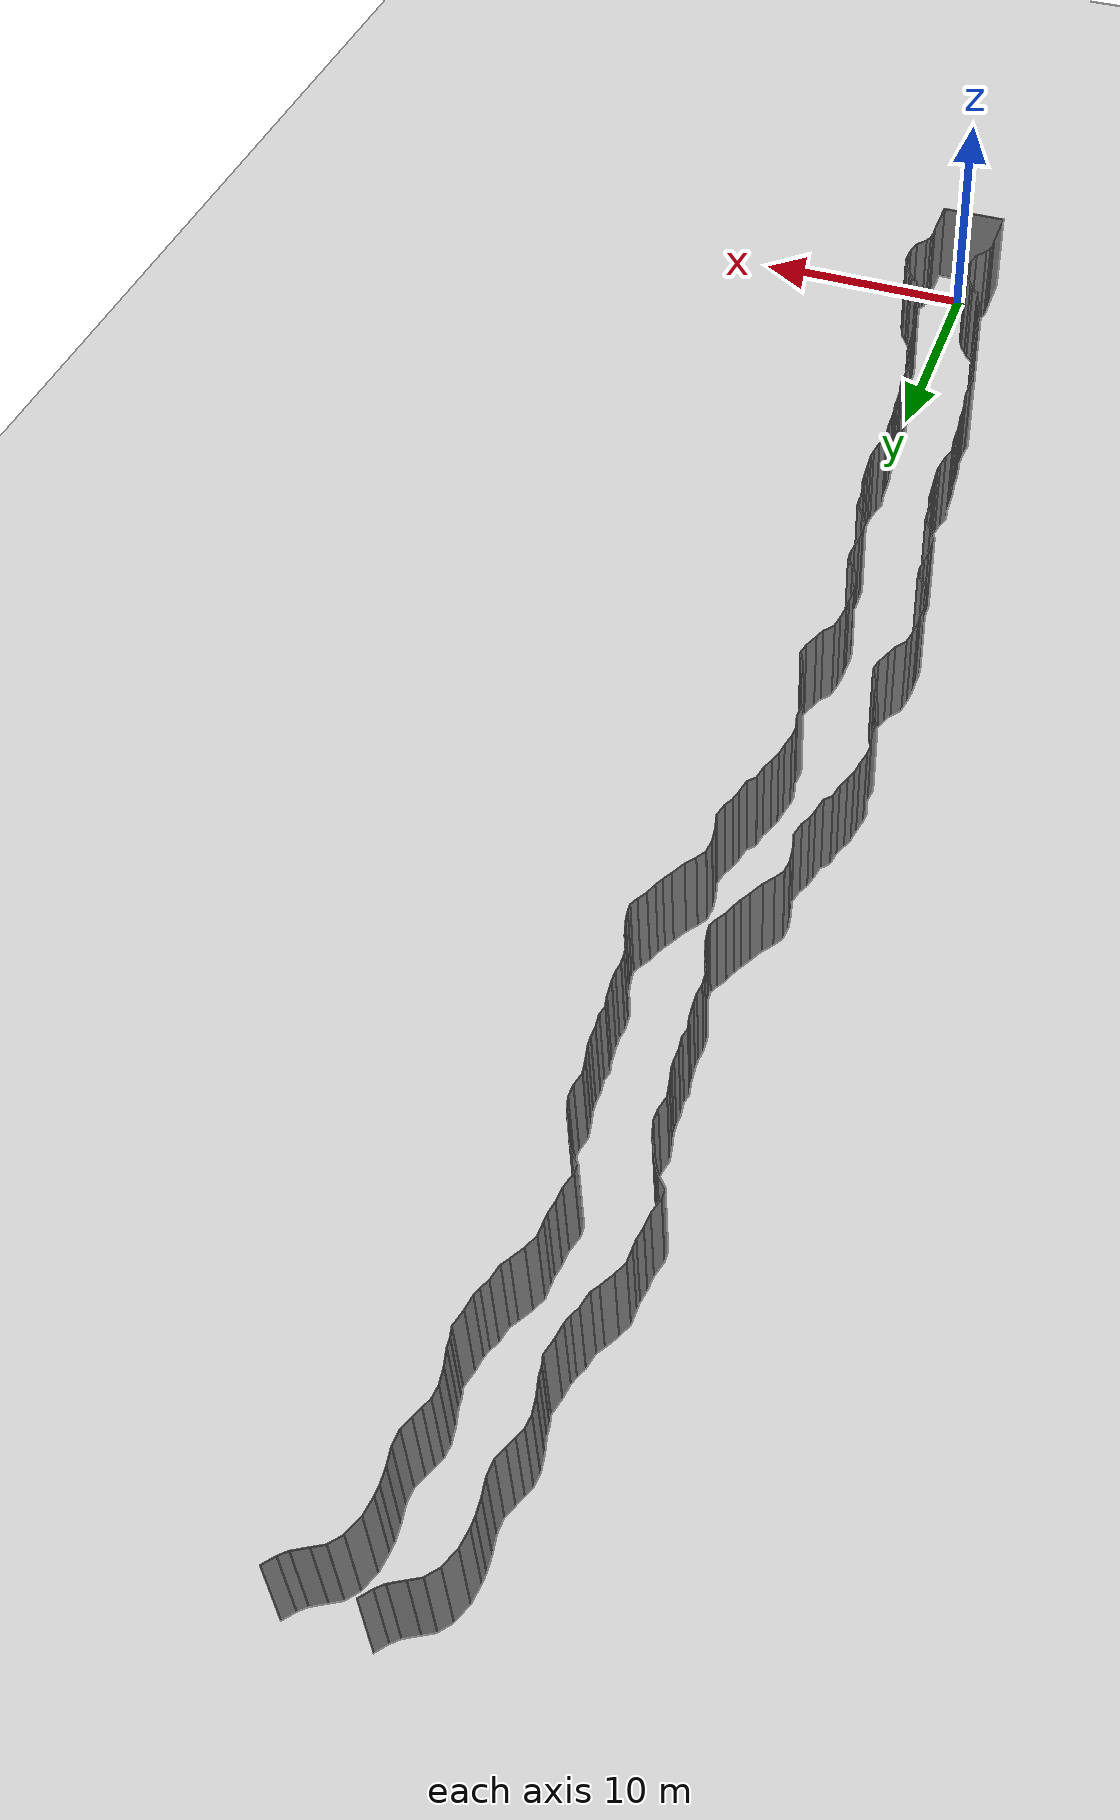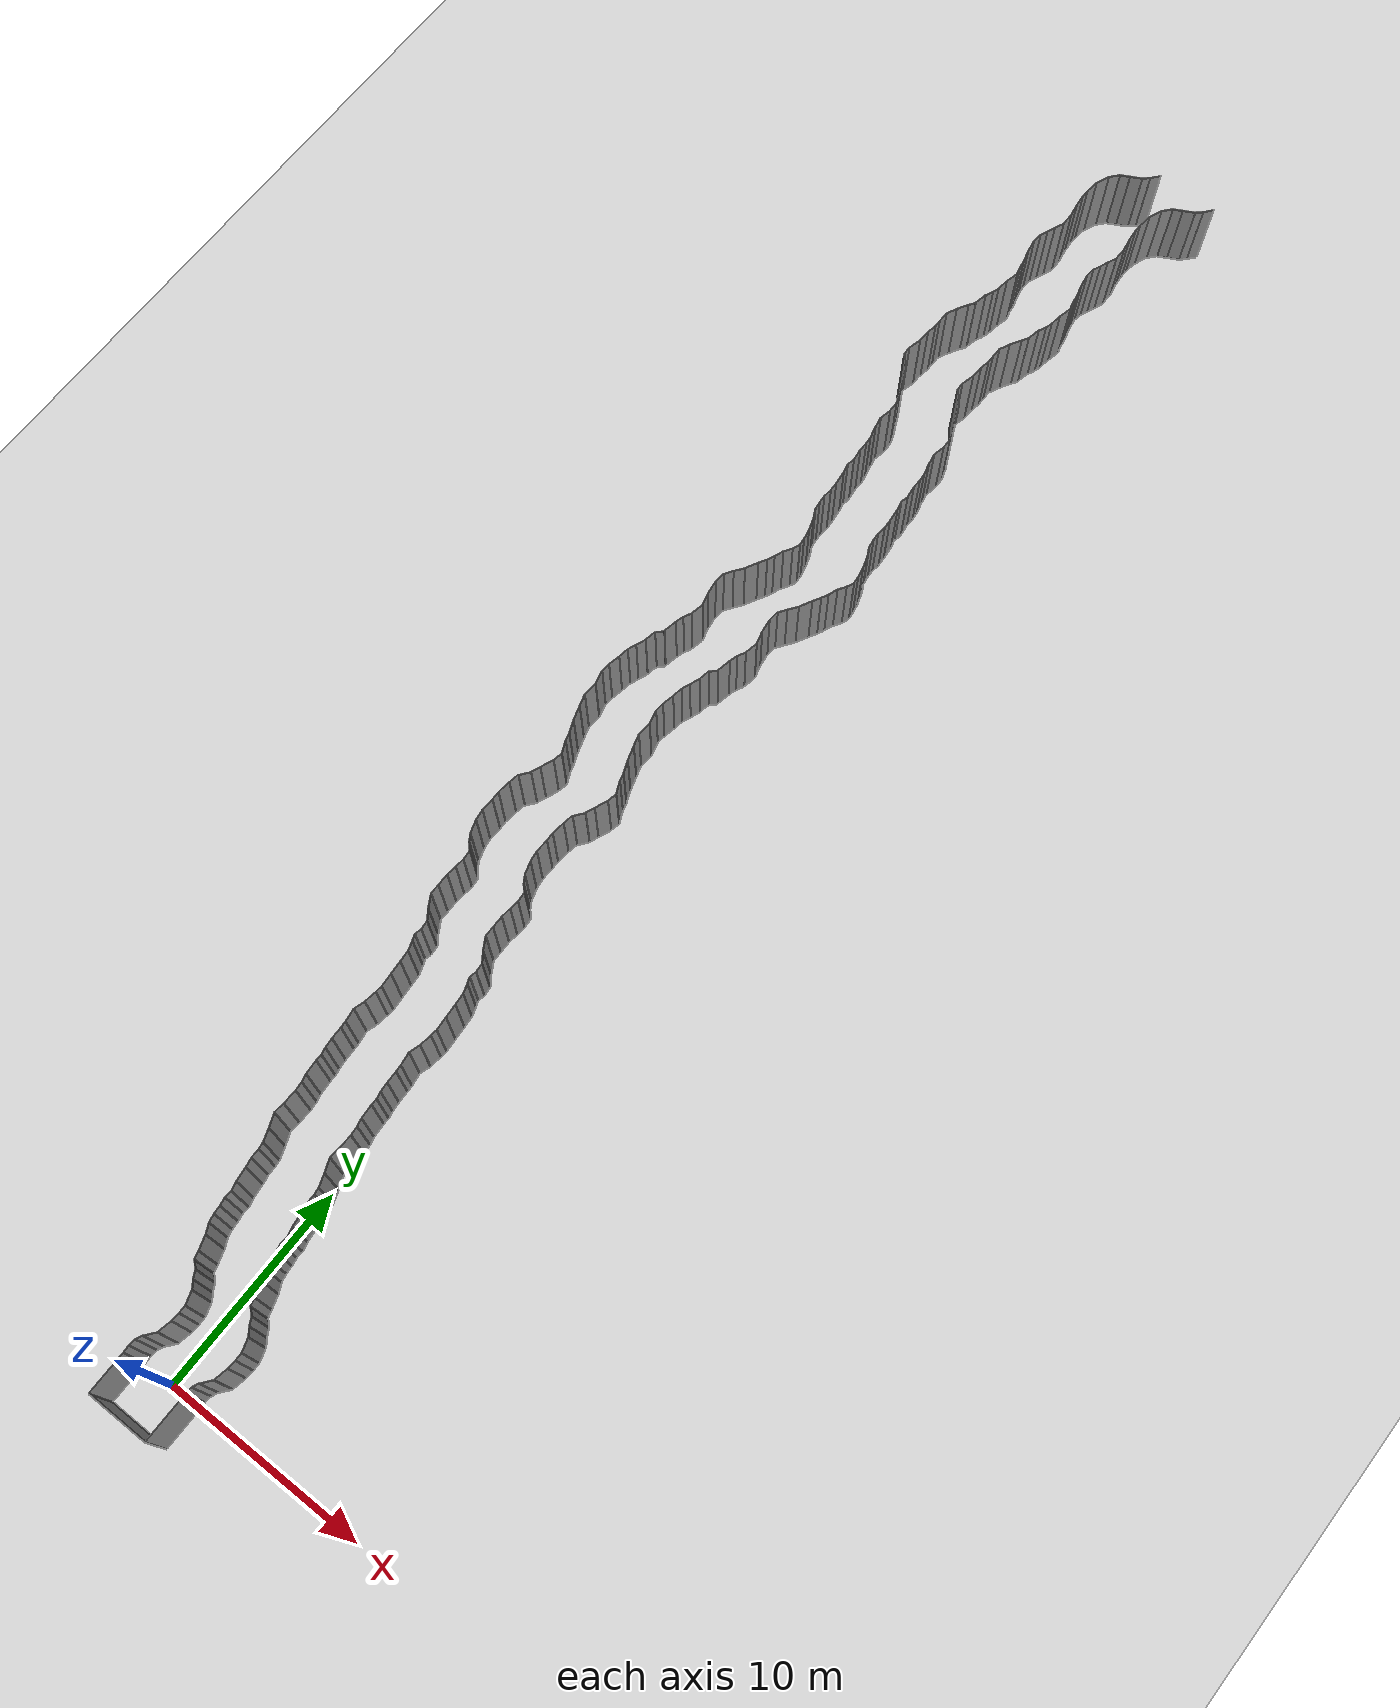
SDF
<sdf version="1.6">
 <world name="default">
  <light name="sun" type="directional">
   <pose>0 0 10 0 -0 0</pose>
   <diffuse>0.8 0.8 0.8 1</diffuse>
   <specular>0.2 0.2 0.2 1</specular>
   <attenuation>
    <range>1000</range>
    <constant>0.9</constant>
    <linear>0.01</linear>
    <quadratic>0.001</quadratic>
   </attenuation>
   <direction>-0.5 0.1 -0.9</direction>
  </light>
  <model name="ground_plane">
   <static>1</static>
   <link name="link">
    <collision name="collision">
     <geometry><plane><normal>0 0 1</normal><size>200 200</size></plane></geometry>
     <surface><friction><ode><mu>100</mu><mu2>50</mu2></ode></friction></surface>
    </collision>
    <visual name="visual">
     <cast_shadows>0</cast_shadows>
     <geometry><plane><normal>0 0 1</normal><size>200 200</size></plane></geometry>
     <material>
      <script><uri>file://media/materials/scripts/gazebo.material</uri><name>Gazebo/Grey</name></script>
     </material>
    </visual>
   </link>
   <pose>0 100 0 0 -0 0</pose>
  </model>
  <gravity>0 0 -9.8</gravity>
  <magnetic_field>6e-06 2.3e-05 -4.2e-05</magnetic_field>
  <atmosphere type="adiabatic"/>
  <physics default="0" name="default_physics" type="ode">
   <max_step_size>0.001</max_step_size>
   <real_time_factor>1</real_time_factor>
   <real_time_update_rate>1000</real_time_update_rate>
  </physics>
  <scene><ambient>0.4 0.4 0.4 1</ambient><background>0.7 0.7 0.7 1</background><shadows>1</shadows></scene>
  <spherical_coordinates>
   <surface_model>EARTH_WGS84</surface_model>
   <latitude_deg>0</latitude_deg>
   <longitude_deg>0</longitude_deg>
   <elevation>0</elevation>
   <heading_deg>0</heading_deg>
  </spherical_coordinates>
  <model name="wall_back">
   <static>1</static>
   <pose>0.0 -2 2 0.0 0 0.0</pose>
   <link name="link">
    <collision name="collision"><geometry><box><size>3 0.02 4</size></box></geometry></collision>
    <visual name="visual">
     <material>
      <script><name>Gazebo/Grey</name><uri>file://media/materials/scripts/gazebo.material</uri></script>
     </material>
     <geometry><box><size>3 0.02 4</size></box></geometry>
    </visual>
   </link>
  </model>
  <model name="wall_left">
   <static>1</static>
   <pose>1.5 -1 2 0 0 0.00</pose>
   <link name="link">
    <collision name="collision"><geometry><box><size>0.02 2 4</size></box></geometry></collision>
    <visual name="visual">
     <material>
      <script><name>Gazebo/Grey</name><uri>file://media/materials/scripts/gazebo.material</uri></script>
     </material>
     <geometry><box><size>0.02 2 4</size></box></geometry>
    </visual>
   </link>
  </model>
  <model name="wall_right">
   <static>1</static>
   <pose>-1.5 -1 2 0 0 0.00</pose>
   <link name="link">
    <collision name="collision"><geometry><box><size>0.02 2 4</size></box></geometry></collision>
    <visual name="visual">
     <material>
      <script><name>Gazebo/Grey</name><uri>file://media/materials/scripts/gazebo.material</uri></script>
     </material>
     <geometry><box><size>0.02 2 4</size></box></geometry>
    </visual>
   </link>
  </model>
  <model name="wall_0">
   <static>1</static>
   <pose>-1.510469168773756 0.1737599955648286 2 0 0 0.06017799457438244</pose>
   <link name="link">
    <collision name="collision"><geometry><box><size>0.02 0.348150194907 4</size></box></geometry></collision>
    <visual name="visual">
     <material>
      <script><name>Gazebo/Grey</name><uri>file://media/materials/scripts/gazebo.material</uri></script>
     </material>
     <geometry><box><size>0.02 0.348150194907 4</size></box></geometry>
    </visual>
   </link>
  </model>
  <model name="wall_1">
   <static>1</static>
   <pose>1.489530831226244 0.1737599955648286 2 0 0 0.06017799457438244</pose>
   <link name="link">
    <collision name="collision"><geometry><box><size>0.02 0.348150194907 4</size></box></geometry></collision>
    <visual name="visual">
     <material>
      <script><name>Gazebo/Grey</name><uri>file://media/materials/scripts/gazebo.material</uri></script>
     </material>
     <geometry><box><size>0.02 0.348150194907 4</size></box></geometry>
    </visual>
   </link>
  </model>
  <model name="wall_2">
   <static>1</static>
   <pose>-1.4994530378009172 0.5157518972264558 2 0 0 -0.12702476339603733</pose>
   <link name="link">
    <collision name="collision"><geometry><box><size>0.02 0.339196652897 4</size></box></geometry></collision>
    <visual name="visual">
     <material>
      <script><name>Gazebo/Grey</name><uri>file://media/materials/scripts/gazebo.material</uri></script>
     </material>
     <geometry><box><size>0.02 0.339196652897 4</size></box></geometry>
    </visual>
   </link>
  </model>
  <model name="wall_3">
   <static>1</static>
   <pose>1.5005469621990828 0.5157518972264558 2 0 0 -0.12702476339603733</pose>
   <link name="link">
    <collision name="collision"><geometry><box><size>0.02 0.339196652897 4</size></box></geometry></collision>
    <visual name="visual">
     <material>
      <script><name>Gazebo/Grey</name><uri>file://media/materials/scripts/gazebo.material</uri></script>
     </material>
     <geometry><box><size>0.02 0.339196652897 4</size></box></geometry>
    </visual>
   </link>
  </model>
  <model name="wall_4">
   <static>1</static>
   <pose>-1.41199776466791 0.828177129915068 2 0 0 -0.4290821500316682</pose>
   <link name="link">
    <collision name="collision"><geometry><box><size>0.02 0.317135635476 4</size></box></geometry></collision>
    <visual name="visual">
     <material>
      <script><name>Gazebo/Grey</name><uri>file://media/materials/scripts/gazebo.material</uri></script>
     </material>
     <geometry><box><size>0.02 0.317135635476 4</size></box></geometry>
    </visual>
   </link>
  </model>
  <model name="wall_5">
   <static>1</static>
   <pose>1.58800223533209 0.828177129915068 2 0 0 -0.4290821500316682</pose>
   <link name="link">
    <collision name="collision"><geometry><box><size>0.02 0.317135635476 4</size></box></geometry></collision>
    <visual name="visual">
     <material>
      <script><name>Gazebo/Grey</name><uri>file://media/materials/scripts/gazebo.material</uri></script>
     </material>
     <geometry><box><size>0.02 0.317135635476 4</size></box></geometry>
    </visual>
   </link>
  </model>
  <model name="wall_6">
   <static>1</static>
   <pose>-1.1598921838826721 1.201235196086324 2 0 0 -0.6827980242633842</pose>
   <link name="link">
    <collision name="collision"><geometry><box><size>0.02 0.590001808012 4</size></box></geometry></collision>
    <visual name="visual">
     <material>
      <script><name>Gazebo/Grey</name><uri>file://media/materials/scripts/gazebo.material</uri></script>
     </material>
     <geometry><box><size>0.02 0.590001808012 4</size></box></geometry>
    </visual>
   </link>
  </model>
  <model name="wall_7">
   <static>1</static>
   <pose>1.8401078161173279 1.201235196086324 2 0 0 -0.6827980242633842</pose>
   <link name="link">
    <collision name="collision"><geometry><box><size>0.02 0.590001808012 4</size></box></geometry></collision>
    <visual name="visual">
     <material>
      <script><name>Gazebo/Grey</name><uri>file://media/materials/scripts/gazebo.material</uri></script>
     </material>
     <geometry><box><size>0.02 0.590001808012 4</size></box></geometry>
    </visual>
   </link>
  </model>
  <model name="wall_8">
   <static>1</static>
   <pose>-0.9057189968333267 1.7638394172357073 2 0 0 -0.2011084965366152</pose>
   <link name="link">
    <collision name="collision"><geometry><box><size>0.02 0.681208202544 4</size></box></geometry></collision>
    <visual name="visual">
     <material>
      <script><name>Gazebo/Grey</name><uri>file://media/materials/scripts/gazebo.material</uri></script>
     </material>
     <geometry><box><size>0.02 0.681208202544 4</size></box></geometry>
    </visual>
   </link>
  </model>
  <model name="wall_9">
   <static>1</static>
   <pose>2.094281003166673 1.7638394172357073 2 0 0 -0.2011084965366152</pose>
   <link name="link">
    <collision name="collision"><geometry><box><size>0.02 0.681208202544 4</size></box></geometry></collision>
    <visual name="visual">
     <material>
      <script><name>Gazebo/Grey</name><uri>file://media/materials/scripts/gazebo.material</uri></script>
     </material>
     <geometry><box><size>0.02 0.681208202544 4</size></box></geometry>
    </visual>
   </link>
  </model>
  <model name="wall_10">
   <static>1</static>
   <pose>-0.8237843901977059 2.3054047616103084 2 0 0 -0.06676921285618291</pose>
   <link name="link">
    <collision name="collision"><geometry><box><size>0.02 0.416579964038 4</size></box></geometry></collision>
    <visual name="visual">
     <material>
      <script><name>Gazebo/Grey</name><uri>file://media/materials/scripts/gazebo.material</uri></script>
     </material>
     <geometry><box><size>0.02 0.416579964038 4</size></box></geometry>
    </visual>
   </link>
  </model>
  <model name="wall_11">
   <static>1</static>
   <pose>2.176215609802294 2.3054047616103084 2 0 0 -0.06676921285618291</pose>
   <link name="link">
    <collision name="collision"><geometry><box><size>0.02 0.416579964038 4</size></box></geometry></collision>
    <visual name="visual">
     <material>
      <script><name>Gazebo/Grey</name><uri>file://media/materials/scripts/gazebo.material</uri></script>
     </material>
     <geometry><box><size>0.02 0.416579964038 4</size></box></geometry>
    </visual>
   </link>
  </model>
  <model name="wall_12">
   <static>1</static>
   <pose>-0.8146648058953255 2.6953685319939176 2 0 0 0.026223796939105346</pose>
   <link name="link">
    <collision name="collision"><geometry><box><size>0.02 0.364401105025 4</size></box></geometry></collision>
    <visual name="visual">
     <material>
      <script><name>Gazebo/Grey</name><uri>file://media/materials/scripts/gazebo.material</uri></script>
     </material>
     <geometry><box><size>0.02 0.364401105025 4</size></box></geometry>
    </visual>
   </link>
  </model>
  <model name="wall_13">
   <static>1</static>
   <pose>2.1853351941046744 2.6953685319939176 2 0 0 0.026223796939105346</pose>
   <link name="link">
    <collision name="collision"><geometry><box><size>0.02 0.364401105025 4</size></box></geometry></collision>
    <visual name="visual">
     <material>
      <script><name>Gazebo/Grey</name><uri>file://media/materials/scripts/gazebo.material</uri></script>
     </material>
     <geometry><box><size>0.02 0.364401105025 4</size></box></geometry>
    </visual>
   </link>
  </model>
  <model name="wall_14">
   <static>1</static>
   <pose>-0.9193898926830465 3.187725549000354 2 0 0 0.31168284968315185</pose>
   <link name="link">
    <collision name="collision"><geometry><box><size>0.02 0.651844850915 4</size></box></geometry></collision>
    <visual name="visual">
     <material>
      <script><name>Gazebo/Grey</name><uri>file://media/materials/scripts/gazebo.material</uri></script>
     </material>
     <geometry><box><size>0.02 0.651844850915 4</size></box></geometry>
    </visual>
   </link>
  </model>
  <model name="wall_15">
   <static>1</static>
   <pose>2.0806101073169536 3.187725549000354 2 0 0 0.31168284968315185</pose>
   <link name="link">
    <collision name="collision"><geometry><box><size>0.02 0.651844850915 4</size></box></geometry></collision>
    <visual name="visual">
     <material>
      <script><name>Gazebo/Grey</name><uri>file://media/materials/scripts/gazebo.material</uri></script>
     </material>
     <geometry><box><size>0.02 0.651844850915 4</size></box></geometry>
    </visual>
   </link>
  </model>
  <model name="wall_16">
   <static>1</static>
   <pose>-1.1455721387722844 3.668385369498843 2 0 0 0.6374814492717766</pose>
   <link name="link">
    <collision name="collision"><geometry><box><size>0.02 0.424194345688 4</size></box></geometry></collision>
    <visual name="visual">
     <material>
      <script><name>Gazebo/Grey</name><uri>file://media/materials/scripts/gazebo.material</uri></script>
     </material>
     <geometry><box><size>0.02 0.424194345688 4</size></box></geometry>
    </visual>
   </link>
  </model>
  <model name="wall_17">
   <static>1</static>
   <pose>1.8544278612277156 3.668385369498843 2 0 0 0.6374814492717766</pose>
   <link name="link">
    <collision name="collision"><geometry><box><size>0.02 0.424194345688 4</size></box></geometry></collision>
    <visual name="visual">
     <material>
      <script><name>Gazebo/Grey</name><uri>file://media/materials/scripts/gazebo.material</uri></script>
     </material>
     <geometry><box><size>0.02 0.424194345688 4</size></box></geometry>
    </visual>
   </link>
  </model>
  <model name="wall_18">
   <static>1</static>
   <pose>-1.3664680322749911 4.014171257539867 2 0 0 0.4950224103680032</pose>
   <link name="link">
    <collision name="collision"><geometry><box><size>0.02 0.398530757652 4</size></box></geometry></collision>
    <visual name="visual">
     <material>
      <script><name>Gazebo/Grey</name><uri>file://media/materials/scripts/gazebo.material</uri></script>
     </material>
     <geometry><box><size>0.02 0.398530757652 4</size></box></geometry>
    </visual>
   </link>
  </model>
  <model name="wall_19">
   <static>1</static>
   <pose>1.6335319677250089 4.014171257539867 2 0 0 0.4950224103680032</pose>
   <link name="link">
    <collision name="collision"><geometry><box><size>0.02 0.398530757652 4</size></box></geometry></collision>
    <visual name="visual">
     <material>
      <script><name>Gazebo/Grey</name><uri>file://media/materials/scripts/gazebo.material</uri></script>
     </material>
     <geometry><box><size>0.02 0.398530757652 4</size></box></geometry>
    </visual>
   </link>
  </model>
  <model name="wall_20">
   <static>1</static>
   <pose>-1.6069622279533375 4.3185332015171225 2 0 0 0.8465050263261898</pose>
   <link name="link">
    <collision name="collision"><geometry><box><size>0.02 0.38942296853 4</size></box></geometry></collision>
    <visual name="visual">
     <material>
      <script><name>Gazebo/Grey</name><uri>file://media/materials/scripts/gazebo.material</uri></script>
     </material>
     <geometry><box><size>0.02 0.38942296853 4</size></box></geometry>
    </visual>
   </link>
  </model>
  <model name="wall_21">
   <static>1</static>
   <pose>1.3930377720466625 4.3185332015171225 2 0 0 0.8465050263261898</pose>
   <link name="link">
    <collision name="collision"><geometry><box><size>0.02 0.38942296853 4</size></box></geometry></collision>
    <visual name="visual">
     <material>
      <script><name>Gazebo/Grey</name><uri>file://media/materials/scripts/gazebo.material</uri></script>
     </material>
     <geometry><box><size>0.02 0.38942296853 4</size></box></geometry>
    </visual>
   </link>
  </model>
  <model name="wall_22">
   <static>1</static>
   <pose>-1.8047803618723768 4.632374893844421 2 0 0 0.27418359341675613</pose>
   <link name="link">
    <collision name="collision"><geometry><box><size>0.02 0.383993318341 4</size></box></geometry></collision>
    <visual name="visual">
     <material>
      <script><name>Gazebo/Grey</name><uri>file://media/materials/scripts/gazebo.material</uri></script>
     </material>
     <geometry><box><size>0.02 0.383993318341 4</size></box></geometry>
    </visual>
   </link>
  </model>
  <model name="wall_23">
   <static>1</static>
   <pose>1.1952196381276232 4.632374893844421 2 0 0 0.27418359341675613</pose>
   <link name="link">
    <collision name="collision"><geometry><box><size>0.02 0.383993318341 4</size></box></geometry></collision>
    <visual name="visual">
     <material>
      <script><name>Gazebo/Grey</name><uri>file://media/materials/scripts/gazebo.material</uri></script>
     </material>
     <geometry><box><size>0.02 0.383993318341 4</size></box></geometry>
    </visual>
   </link>
  </model>
  <model name="wall_24">
   <static>1</static>
   <pose>-1.963753511820921 5.145152706719379 2 0 0 0.3153435752088974</pose>
   <link name="link">
    <collision name="collision"><geometry><box><size>0.02 0.689926116398 4</size></box></geometry></collision>
    <visual name="visual">
     <material>
      <script><name>Gazebo/Grey</name><uri>file://media/materials/scripts/gazebo.material</uri></script>
     </material>
     <geometry><box><size>0.02 0.689926116398 4</size></box></geometry>
    </visual>
   </link>
  </model>
  <model name="wall_25">
   <static>1</static>
   <pose>1.036246488179079 5.145152706719379 2 0 0 0.3153435752088974</pose>
   <link name="link">
    <collision name="collision"><geometry><box><size>0.02 0.689926116398 4</size></box></geometry></collision>
    <visual name="visual">
     <material>
      <script><name>Gazebo/Grey</name><uri>file://media/materials/scripts/gazebo.material</uri></script>
     </material>
     <geometry><box><size>0.02 0.689926116398 4</size></box></geometry>
    </visual>
   </link>
  </model>
  <model name="wall_26">
   <static>1</static>
   <pose>-2.1779065068808707 5.694591785305188 2 0 0 0.450640609318869</pose>
   <link name="link">
    <collision name="collision"><geometry><box><size>0.02 0.492099526882 4</size></box></geometry></collision>
    <visual name="visual">
     <material>
      <script><name>Gazebo/Grey</name><uri>file://media/materials/scripts/gazebo.material</uri></script>
     </material>
     <geometry><box><size>0.02 0.492099526882 4</size></box></geometry>
    </visual>
   </link>
  </model>
  <model name="wall_27">
   <static>1</static>
   <pose>0.8220934931191293 5.694591785305188 2 0 0 0.450640609318869</pose>
   <link name="link">
    <collision name="collision"><geometry><box><size>0.02 0.492099526882 4</size></box></geometry></collision>
    <visual name="visual">
     <material>
      <script><name>Gazebo/Grey</name><uri>file://media/materials/scripts/gazebo.material</uri></script>
     </material>
     <geometry><box><size>0.02 0.492099526882 4</size></box></geometry>
    </visual>
   </link>
  </model>
  <model name="wall_28">
   <static>1</static>
   <pose>-2.32236321173488 6.109094926779471 2 0 0 0.19085240196837205</pose>
   <link name="link">
    <collision name="collision"><geometry><box><size>0.02 0.393172780468 4</size></box></geometry></collision>
    <visual name="visual">
     <material>
      <script><name>Gazebo/Grey</name><uri>file://media/materials/scripts/gazebo.material</uri></script>
     </material>
     <geometry><box><size>0.02 0.393172780468 4</size></box></geometry>
    </visual>
   </link>
  </model>
  <model name="wall_29">
   <static>1</static>
   <pose>0.67763678826512 6.109094926779471 2 0 0 0.19085240196837205</pose>
   <link name="link">
    <collision name="collision"><geometry><box><size>0.02 0.393172780468 4</size></box></geometry></collision>
    <visual name="visual">
     <material>
      <script><name>Gazebo/Grey</name><uri>file://media/materials/scripts/gazebo.material</uri></script>
     </material>
     <geometry><box><size>0.02 0.393172780468 4</size></box></geometry>
    </visual>
   </link>
  </model>
  <model name="wall_30">
   <static>1</static>
   <pose>-2.374198630573105 6.495337697885498 2 0 0 0.07512669214178795</pose>
   <link name="link">
    <collision name="collision"><geometry><box><size>0.02 0.387544782264 4</size></box></geometry></collision>
    <visual name="visual">
     <material>
      <script><name>Gazebo/Grey</name><uri>file://media/materials/scripts/gazebo.material</uri></script>
     </material>
     <geometry><box><size>0.02 0.387544782264 4</size></box></geometry>
    </visual>
   </link>
  </model>
  <model name="wall_31">
   <static>1</static>
   <pose>0.6258013694268949 6.495337697885498 2 0 0 0.07512669214178795</pose>
   <link name="link">
    <collision name="collision"><geometry><box><size>0.02 0.387544782264 4</size></box></geometry></collision>
    <visual name="visual">
     <material>
      <script><name>Gazebo/Grey</name><uri>file://media/materials/scripts/gazebo.material</uri></script>
     </material>
     <geometry><box><size>0.02 0.387544782264 4</size></box></geometry>
    </visual>
   </link>
  </model>
  <model name="wall_32">
   <static>1</static>
   <pose>-2.4218261019833407 6.88067813417852 2 0 0 0.17053539702044512</pose>
   <link name="link">
    <collision name="collision"><geometry><box><size>0.02 0.389884883473 4</size></box></geometry></collision>
    <visual name="visual">
     <material>
      <script><name>Gazebo/Grey</name><uri>file://media/materials/scripts/gazebo.material</uri></script>
     </material>
     <geometry><box><size>0.02 0.389884883473 4</size></box></geometry>
    </visual>
   </link>
  </model>
  <model name="wall_33">
   <static>1</static>
   <pose>0.5781738980166593 6.88067813417852 2 0 0 0.17053539702044512</pose>
   <link name="link">
    <collision name="collision"><geometry><box><size>0.02 0.389884883473 4</size></box></geometry></collision>
    <visual name="visual">
     <material>
      <script><name>Gazebo/Grey</name><uri>file://media/materials/scripts/gazebo.material</uri></script>
     </material>
     <geometry><box><size>0.02 0.389884883473 4</size></box></geometry>
    </visual>
   </link>
  </model>
  <model name="wall_34">
   <static>1</static>
   <pose>-2.4358964294610845 7.2439056489470754 2 0 0 -0.11066190136848338</pose>
   <link name="link">
    <collision name="collision"><geometry><box><size>0.02 0.34433200213 4</size></box></geometry></collision>
    <visual name="visual">
     <material>
      <script><name>Gazebo/Grey</name><uri>file://media/materials/scripts/gazebo.material</uri></script>
     </material>
     <geometry><box><size>0.02 0.34433200213 4</size></box></geometry>
    </visual>
   </link>
  </model>
  <model name="wall_35">
   <static>1</static>
   <pose>0.5641035705389155 7.2439056489470754 2 0 0 -0.11066190136848338</pose>
   <link name="link">
    <collision name="collision"><geometry><box><size>0.02 0.34433200213 4</size></box></geometry></collision>
    <visual name="visual">
     <material>
      <script><name>Gazebo/Grey</name><uri>file://media/materials/scripts/gazebo.material</uri></script>
     </material>
     <geometry><box><size>0.02 0.34433200213 4</size></box></geometry>
    </visual>
   </link>
  </model>
  <model name="wall_36">
   <static>1</static>
   <pose>-2.471697332495646 7.624812421858121 2 0 0 0.255563577798341</pose>
   <link name="link">
    <collision name="collision"><geometry><box><size>0.02 0.433673021365 4</size></box></geometry></collision>
    <visual name="visual">
     <material>
      <script><name>Gazebo/Grey</name><uri>file://media/materials/scripts/gazebo.material</uri></script>
     </material>
     <geometry><box><size>0.02 0.433673021365 4</size></box></geometry>
    </visual>
   </link>
  </model>
  <model name="wall_37">
   <static>1</static>
   <pose>0.5283026675043541 7.624812421858121 2 0 0 0.255563577798341</pose>
   <link name="link">
    <collision name="collision"><geometry><box><size>0.02 0.433673021365 4</size></box></geometry></collision>
    <visual name="visual">
     <material>
      <script><name>Gazebo/Grey</name><uri>file://media/materials/scripts/gazebo.material</uri></script>
     </material>
     <geometry><box><size>0.02 0.433673021365 4</size></box></geometry>
    </visual>
   </link>
  </model>
  <model name="wall_38">
   <static>1</static>
   <pose>-2.5685930408816215 8.171645667004977 2 0 0 0.12421339007388195</pose>
   <link name="link">
    <collision name="collision"><geometry><box><size>0.02 0.679312553434 4</size></box></geometry></collision>
    <visual name="visual">
     <material>
      <script><name>Gazebo/Grey</name><uri>file://media/materials/scripts/gazebo.material</uri></script>
     </material>
     <geometry><box><size>0.02 0.679312553434 4</size></box></geometry>
    </visual>
   </link>
  </model>
  <model name="wall_39">
   <static>1</static>
   <pose>0.43140695911837845 8.171645667004977 2 0 0 0.12421339007388195</pose>
   <link name="link">
    <collision name="collision"><geometry><box><size>0.02 0.679312553434 4</size></box></geometry></collision>
    <visual name="visual">
     <material>
      <script><name>Gazebo/Grey</name><uri>file://media/materials/scripts/gazebo.material</uri></script>
     </material>
     <geometry><box><size>0.02 0.679312553434 4</size></box></geometry>
    </visual>
   </link>
  </model>
  <model name="wall_40">
   <static>1</static>
   <pose>-2.649137019150533 8.720029882270513 2 0 0 0.18001926450939906</pose>
   <link name="link">
    <collision name="collision"><geometry><box><size>0.02 0.429632443371 4</size></box></geometry></collision>
    <visual name="visual">
     <material>
      <script><name>Gazebo/Grey</name><uri>file://media/materials/scripts/gazebo.material</uri></script>
     </material>
     <geometry><box><size>0.02 0.429632443371 4</size></box></geometry>
    </visual>
   </link>
  </model>
  <model name="wall_41">
   <static>1</static>
   <pose>0.3508629808494672 8.720029882270513 2 0 0 0.18001926450939906</pose>
   <link name="link">
    <collision name="collision"><geometry><box><size>0.02 0.429632443371 4</size></box></geometry></collision>
    <visual name="visual">
     <material>
      <script><name>Gazebo/Grey</name><uri>file://media/materials/scripts/gazebo.material</uri></script>
     </material>
     <geometry><box><size>0.02 0.429632443371 4</size></box></geometry>
    </visual>
   </link>
  </model>
  <model name="wall_42">
   <static>1</static>
   <pose>-2.6891948705922246 9.158319777123236 2 0 0 0.007029442426870586</pose>
   <link name="link">
    <collision name="collision"><geometry><box><size>0.02 0.453901316203 4</size></box></geometry></collision>
    <visual name="visual">
     <material>
      <script><name>Gazebo/Grey</name><uri>file://media/materials/scripts/gazebo.material</uri></script>
     </material>
     <geometry><box><size>0.02 0.453901316203 4</size></box></geometry>
    </visual>
   </link>
  </model>
  <model name="wall_43">
   <static>1</static>
   <pose>0.3108051294077754 9.158319777123236 2 0 0 0.007029442426870586</pose>
   <link name="link">
    <collision name="collision"><geometry><box><size>0.02 0.453901316203 4</size></box></geometry></collision>
    <visual name="visual">
     <material>
      <script><name>Gazebo/Grey</name><uri>file://media/materials/scripts/gazebo.material</uri></script>
     </material>
     <geometry><box><size>0.02 0.453901316203 4</size></box></geometry>
    </visual>
   </link>
  </model>
  <model name="wall_44">
   <static>1</static>
   <pose>-2.713628992946866 9.540722898319459 2 0 0 0.1458694389386923</pose>
   <link name="link">
    <collision name="collision"><geometry><box><size>0.02 0.314253543094 4</size></box></geometry></collision>
    <visual name="visual">
     <material>
      <script><name>Gazebo/Grey</name><uri>file://media/materials/scripts/gazebo.material</uri></script>
     </material>
     <geometry><box><size>0.02 0.314253543094 4</size></box></geometry>
    </visual>
   </link>
  </model>
  <model name="wall_45">
   <static>1</static>
   <pose>0.286371007053134 9.540722898319459 2 0 0 0.1458694389386923</pose>
   <link name="link">
    <collision name="collision"><geometry><box><size>0.02 0.314253543094 4</size></box></geometry></collision>
    <visual name="visual">
     <material>
      <script><name>Gazebo/Grey</name><uri>file://media/materials/scripts/gazebo.material</uri></script>
     </material>
     <geometry><box><size>0.02 0.314253543094 4</size></box></geometry>
    </visual>
   </link>
  </model>
  <model name="wall_46">
   <static>1</static>
   <pose>-2.8413232840923013 9.992477060414144 2 0 0 0.3401338914865158</pose>
   <link name="link">
    <collision name="collision"><geometry><box><size>0.02 0.628604957994 4</size></box></geometry></collision>
    <visual name="visual">
     <material>
      <script><name>Gazebo/Grey</name><uri>file://media/materials/scripts/gazebo.material</uri></script>
     </material>
     <geometry><box><size>0.02 0.628604957994 4</size></box></geometry>
    </visual>
   </link>
  </model>
  <model name="wall_47">
   <static>1</static>
   <pose>0.15867671590769872 9.992477060414144 2 0 0 0.3401338914865158</pose>
   <link name="link">
    <collision name="collision"><geometry><box><size>0.02 0.628604957994 4</size></box></geometry></collision>
    <visual name="visual">
     <material>
      <script><name>Gazebo/Grey</name><uri>file://media/materials/scripts/gazebo.material</uri></script>
     </material>
     <geometry><box><size>0.02 0.628604957994 4</size></box></geometry>
    </visual>
   </link>
  </model>
  <model name="wall_48">
   <static>1</static>
   <pose>-3.069808783457443 10.599638395436024 2 0 0 0.3785189918229561</pose>
   <link name="link">
    <collision name="collision"><geometry><box><size>0.02 0.669093649854 4</size></box></geometry></collision>
    <visual name="visual">
     <material>
      <script><name>Gazebo/Grey</name><uri>file://media/materials/scripts/gazebo.material</uri></script>
     </material>
     <geometry><box><size>0.02 0.669093649854 4</size></box></geometry>
    </visual>
   </link>
  </model>
  <model name="wall_49">
   <static>1</static>
   <pose>-0.06980878345744301 10.599638395436024 2 0 0 0.3785189918229561</pose>
   <link name="link">
    <collision name="collision"><geometry><box><size>0.02 0.669093649854 4</size></box></geometry></collision>
    <visual name="visual">
     <material>
      <script><name>Gazebo/Grey</name><uri>file://media/materials/scripts/gazebo.material</uri></script>
     </material>
     <geometry><box><size>0.02 0.669093649854 4</size></box></geometry>
    </visual>
   </link>
  </model>
  <model name="wall_50">
   <static>1</static>
   <pose>-3.162965105965186 11.16699354636697 2 0 0 -0.11825611039666503</pose>
   <link name="link">
    <collision name="collision"><geometry><box><size>0.02 0.516587720495 4</size></box></geometry></collision>
    <visual name="visual">
     <material>
      <script><name>Gazebo/Grey</name><uri>file://media/materials/scripts/gazebo.material</uri></script>
     </material>
     <geometry><box><size>0.02 0.516587720495 4</size></box></geometry>
    </visual>
   </link>
  </model>
  <model name="wall_51">
   <static>1</static>
   <pose>-0.1629651059651862 11.16699354636697 2 0 0 -0.11825611039666503</pose>
   <link name="link">
    <collision name="collision"><geometry><box><size>0.02 0.516587720495 4</size></box></geometry></collision>
    <visual name="visual">
     <material>
      <script><name>Gazebo/Grey</name><uri>file://media/materials/scripts/gazebo.material</uri></script>
     </material>
     <geometry><box><size>0.02 0.516587720495 4</size></box></geometry>
    </visual>
   </link>
  </model>
  <model name="wall_52">
   <static>1</static>
   <pose>-3.121385192332371 11.772022477766635 2 0 0 -0.031854316212388885</pose>
   <link name="link">
    <collision name="collision"><geometry><box><size>0.02 0.697431858511 4</size></box></geometry></collision>
    <visual name="visual">
     <material>
      <script><name>Gazebo/Grey</name><uri>file://media/materials/scripts/gazebo.material</uri></script>
     </material>
     <geometry><box><size>0.02 0.697431858511 4</size></box></geometry>
    </visual>
   </link>
  </model>
  <model name="wall_53">
   <static>1</static>
   <pose>-0.121385192332371 11.772022477766635 2 0 0 -0.031854316212388885</pose>
   <link name="link">
    <collision name="collision"><geometry><box><size>0.02 0.697431858511 4</size></box></geometry></collision>
    <visual name="visual">
     <material>
      <script><name>Gazebo/Grey</name><uri>file://media/materials/scripts/gazebo.material</uri></script>
     </material>
     <geometry><box><size>0.02 0.697431858511 4</size></box></geometry>
    </visual>
   </link>
  </model>
  <model name="wall_54">
   <static>1</static>
   <pose>-3.1298766354527037 12.33436319061964 2 0 0 0.09140741682924972</pose>
   <link name="link">
    <collision name="collision"><geometry><box><size>0.02 0.429395999363 4</size></box></geometry></collision>
    <visual name="visual">
     <material>
      <script><name>Gazebo/Grey</name><uri>file://media/materials/scripts/gazebo.material</uri></script>
     </material>
     <geometry><box><size>0.02 0.429395999363 4</size></box></geometry>
    </visual>
   </link>
  </model>
  <model name="wall_55">
   <static>1</static>
   <pose>-0.12987663545270367 12.33436319061964 2 0 0 0.09140741682924972</pose>
   <link name="link">
    <collision name="collision"><geometry><box><size>0.02 0.429395999363 4</size></box></geometry></collision>
    <visual name="visual">
     <material>
      <script><name>Gazebo/Grey</name><uri>file://media/materials/scripts/gazebo.material</uri></script>
     </material>
     <geometry><box><size>0.02 0.429395999363 4</size></box></geometry>
    </visual>
   </link>
  </model>
  <model name="wall_56">
   <static>1</static>
   <pose>-3.1899851738225578 12.729374305036183 2 0 0 0.21994176333821663</pose>
   <link name="link">
    <collision name="collision"><geometry><box><size>0.02 0.371364974453 4</size></box></geometry></collision>
    <visual name="visual">
     <material>
      <script><name>Gazebo/Grey</name><uri>file://media/materials/scripts/gazebo.material</uri></script>
     </material>
     <geometry><box><size>0.02 0.371364974453 4</size></box></geometry>
    </visual>
   </link>
  </model>
  <model name="wall_57">
   <static>1</static>
   <pose>-0.18998517382255775 12.729374305036183 2 0 0 0.21994176333821663</pose>
   <link name="link">
    <collision name="collision"><geometry><box><size>0.02 0.371364974453 4</size></box></geometry></collision>
    <visual name="visual">
     <material>
      <script><name>Gazebo/Grey</name><uri>file://media/materials/scripts/gazebo.material</uri></script>
     </material>
     <geometry><box><size>0.02 0.371364974453 4</size></box></geometry>
    </visual>
   </link>
  </model>
  <model name="wall_58">
   <static>1</static>
   <pose>-3.2531646637233225 13.25227475203064 2 0 0 0.06624538680910196</pose>
   <link name="link">
    <collision name="collision"><geometry><box><size>0.02 0.684884284759 4</size></box></geometry></collision>
    <visual name="visual">
     <material>
      <script><name>Gazebo/Grey</name><uri>file://media/materials/scripts/gazebo.material</uri></script>
     </material>
     <geometry><box><size>0.02 0.684884284759 4</size></box></geometry>
    </visual>
   </link>
  </model>
  <model name="wall_59">
   <static>1</static>
   <pose>-0.25316466372332247 13.25227475203064 2 0 0 0.06624538680910196</pose>
   <link name="link">
    <collision name="collision"><geometry><box><size>0.02 0.684884284759 4</size></box></geometry></collision>
    <visual name="visual">
     <material>
      <script><name>Gazebo/Grey</name><uri>file://media/materials/scripts/gazebo.material</uri></script>
     </material>
     <geometry><box><size>0.02 0.684884284759 4</size></box></geometry>
    </visual>
   </link>
  </model>
  <model name="wall_60">
   <static>1</static>
   <pose>-3.272919042660725 13.74881881598639 2 0 0 -0.018817200569160534</pose>
   <link name="link">
    <collision name="collision"><geometry><box><size>0.02 0.309760923857 4</size></box></geometry></collision>
    <visual name="visual">
     <material>
      <script><name>Gazebo/Grey</name><uri>file://media/materials/scripts/gazebo.material</uri></script>
     </material>
     <geometry><box><size>0.02 0.309760923857 4</size></box></geometry>
    </visual>
   </link>
  </model>
  <model name="wall_61">
   <static>1</static>
   <pose>-0.2729190426607251 13.74881881598639 2 0 0 -0.018817200569160534</pose>
   <link name="link">
    <collision name="collision"><geometry><box><size>0.02 0.309760923857 4</size></box></geometry></collision>
    <visual name="visual">
     <material>
      <script><name>Gazebo/Grey</name><uri>file://media/materials/scripts/gazebo.material</uri></script>
     </material>
     <geometry><box><size>0.02 0.309760923857 4</size></box></geometry>
    </visual>
   </link>
  </model>
  <model name="wall_62">
   <static>1</static>
   <pose>-3.3021814037474555 14.066867854048839 2 0 0 0.19466851493078532</pose>
   <link name="link">
    <collision name="collision"><geometry><box><size>0.02 0.332675620036 4</size></box></geometry></collision>
    <visual name="visual">
     <material>
      <script><name>Gazebo/Grey</name><uri>file://media/materials/scripts/gazebo.material</uri></script>
     </material>
     <geometry><box><size>0.02 0.332675620036 4</size></box></geometry>
    </visual>
   </link>
  </model>
  <model name="wall_63">
   <static>1</static>
   <pose>-0.3021814037474555 14.066867854048839 2 0 0 0.19466851493078532</pose>
   <link name="link">
    <collision name="collision"><geometry><box><size>0.02 0.332675620036 4</size></box></geometry></collision>
    <visual name="visual">
     <material>
      <script><name>Gazebo/Grey</name><uri>file://media/materials/scripts/gazebo.material</uri></script>
     </material>
     <geometry><box><size>0.02 0.332675620036 4</size></box></geometry>
    </visual>
   </link>
  </model>
  <model name="wall_64">
   <static>1</static>
   <pose>-3.3541571712531906 14.462953008625506 2 0 0 0.0848114500214876</pose>
   <link name="link">
    <collision name="collision"><geometry><box><size>0.02 0.467458520212 4</size></box></geometry></collision>
    <visual name="visual">
     <material>
      <script><name>Gazebo/Grey</name><uri>file://media/materials/scripts/gazebo.material</uri></script>
     </material>
     <geometry><box><size>0.02 0.467458520212 4</size></box></geometry>
    </visual>
   </link>
  </model>
  <model name="wall_65">
   <static>1</static>
   <pose>-0.3541571712531906 14.462953008625506 2 0 0 0.0848114500214876</pose>
   <link name="link">
    <collision name="collision"><geometry><box><size>0.02 0.467458520212 4</size></box></geometry></collision>
    <visual name="visual">
     <material>
      <script><name>Gazebo/Grey</name><uri>file://media/materials/scripts/gazebo.material</uri></script>
     </material>
     <geometry><box><size>0.02 0.467458520212 4</size></box></geometry>
    </visual>
   </link>
  </model>
  <model name="wall_66">
   <static>1</static>
   <pose>-3.3794987564947947 14.982548874729329 2 0 0 0.0193289279880764</pose>
   <link name="link">
    <collision name="collision"><geometry><box><size>0.02 0.573520547309 4</size></box></geometry></collision>
    <visual name="visual">
     <material>
      <script><name>Gazebo/Grey</name><uri>file://media/materials/scripts/gazebo.material</uri></script>
     </material>
     <geometry><box><size>0.02 0.573520547309 4</size></box></geometry>
    </visual>
   </link>
  </model>
  <model name="wall_67">
   <static>1</static>
   <pose>-0.3794987564947947 14.982548874729329 2 0 0 0.0193289279880764</pose>
   <link name="link">
    <collision name="collision"><geometry><box><size>0.02 0.573520547309 4</size></box></geometry></collision>
    <visual name="visual">
     <material>
      <script><name>Gazebo/Grey</name><uri>file://media/materials/scripts/gazebo.material</uri></script>
     </material>
     <geometry><box><size>0.02 0.573520547309 4</size></box></geometry>
    </visual>
   </link>
  </model>
  <model name="wall_68">
   <static>1</static>
   <pose>-3.394325481687707 15.425965754648598 2 0 0 0.05917587708723591</pose>
   <link name="link">
    <collision name="collision"><geometry><box><size>0.02 0.313969912045 4</size></box></geometry></collision>
    <visual name="visual">
     <material>
      <script><name>Gazebo/Grey</name><uri>file://media/materials/scripts/gazebo.material</uri></script>
     </material>
     <geometry><box><size>0.02 0.313969912045 4</size></box></geometry>
    </visual>
   </link>
  </model>
  <model name="wall_69">
   <static>1</static>
   <pose>-0.39432548168770687 15.425965754648598 2 0 0 0.05917587708723591</pose>
   <link name="link">
    <collision name="collision"><geometry><box><size>0.02 0.313969912045 4</size></box></geometry></collision>
    <visual name="visual">
     <material>
      <script><name>Gazebo/Grey</name><uri>file://media/materials/scripts/gazebo.material</uri></script>
     </material>
     <geometry><box><size>0.02 0.313969912045 4</size></box></geometry>
    </visual>
   </link>
  </model>
  <model name="wall_70">
   <static>1</static>
   <pose>-3.4475898272669308 15.893274666819671 2 0 0 0.14066251025544266</pose>
   <link name="link">
    <collision name="collision"><geometry><box><size>0.02 0.627394043194 4</size></box></geometry></collision>
    <visual name="visual">
     <material>
      <script><name>Gazebo/Grey</name><uri>file://media/materials/scripts/gazebo.material</uri></script>
     </material>
     <geometry><box><size>0.02 0.627394043194 4</size></box></geometry>
    </visual>
   </link>
  </model>
  <model name="wall_71">
   <static>1</static>
   <pose>-0.44758982726693075 15.893274666819671 2 0 0 0.14066251025544266</pose>
   <link name="link">
    <collision name="collision"><geometry><box><size>0.02 0.627394043194 4</size></box></geometry></collision>
    <visual name="visual">
     <material>
      <script><name>Gazebo/Grey</name><uri>file://media/materials/scripts/gazebo.material</uri></script>
     </material>
     <geometry><box><size>0.02 0.627394043194 4</size></box></geometry>
    </visual>
   </link>
  </model>
  <model name="wall_72">
   <static>1</static>
   <pose>-3.411470448055781 16.46128203625656 2 0 0 -0.3016783330120834</pose>
   <link name="link">
    <collision name="collision"><geometry><box><size>0.02 0.53916646876 4</size></box></geometry></collision>
    <visual name="visual">
     <material>
      <script><name>Gazebo/Grey</name><uri>file://media/materials/scripts/gazebo.material</uri></script>
     </material>
     <geometry><box><size>0.02 0.53916646876 4</size></box></geometry>
    </visual>
   </link>
  </model>
  <model name="wall_73">
   <static>1</static>
   <pose>-0.4114704480557809 16.46128203625656 2 0 0 -0.3016783330120834</pose>
   <link name="link">
    <collision name="collision"><geometry><box><size>0.02 0.53916646876 4</size></box></geometry></collision>
    <visual name="visual">
     <material>
      <script><name>Gazebo/Grey</name><uri>file://media/materials/scripts/gazebo.material</uri></script>
     </material>
     <geometry><box><size>0.02 0.53916646876 4</size></box></geometry>
    </visual>
   </link>
  </model>
  <model name="wall_74">
   <static>1</static>
   <pose>-3.2860115752755705 17.01383835826963 2 0 0 -0.15249082622703872</pose>
   <link name="link">
    <collision name="collision"><geometry><box><size>0.02 0.5972257192 4</size></box></geometry></collision>
    <visual name="visual">
     <material>
      <script><name>Gazebo/Grey</name><uri>file://media/materials/scripts/gazebo.material</uri></script>
     </material>
     <geometry><box><size>0.02 0.5972257192 4</size></box></geometry>
    </visual>
   </link>
  </model>
  <model name="wall_75">
   <static>1</static>
   <pose>-0.28601157527557053 17.01383835826963 2 0 0 -0.15249082622703872</pose>
   <link name="link">
    <collision name="collision"><geometry><box><size>0.02 0.5972257192 4</size></box></geometry></collision>
    <visual name="visual">
     <material>
      <script><name>Gazebo/Grey</name><uri>file://media/materials/scripts/gazebo.material</uri></script>
     </material>
     <geometry><box><size>0.02 0.5972257192 4</size></box></geometry>
    </visual>
   </link>
  </model>
  <model name="wall_76">
   <static>1</static>
   <pose>-3.222303903417434 17.472723167792196 2 0 0 -0.11159348052013675</pose>
   <link name="link">
    <collision name="collision"><geometry><box><size>0.02 0.329523904005 4</size></box></geometry></collision>
    <visual name="visual">
     <material>
      <script><name>Gazebo/Grey</name><uri>file://media/materials/scripts/gazebo.material</uri></script>
     </material>
     <geometry><box><size>0.02 0.329523904005 4</size></box></geometry>
    </visual>
   </link>
  </model>
  <model name="wall_77">
   <static>1</static>
   <pose>-0.2223039034174339 17.472723167792196 2 0 0 -0.11159348052013675</pose>
   <link name="link">
    <collision name="collision"><geometry><box><size>0.02 0.329523904005 4</size></box></geometry></collision>
    <visual name="visual">
     <material>
      <script><name>Gazebo/Grey</name><uri>file://media/materials/scripts/gazebo.material</uri></script>
     </material>
     <geometry><box><size>0.02 0.329523904005 4</size></box></geometry>
    </visual>
   </link>
  </model>
  <model name="wall_78">
   <static>1</static>
   <pose>-3.226909889007271 17.96044130256942 2 0 0 0.07073227570332395</pose>
   <link name="link">
    <collision name="collision"><geometry><box><size>0.02 0.649586315642 4</size></box></geometry></collision>
    <visual name="visual">
     <material>
      <script><name>Gazebo/Grey</name><uri>file://media/materials/scripts/gazebo.material</uri></script>
     </material>
     <geometry><box><size>0.02 0.649586315642 4</size></box></geometry>
    </visual>
   </link>
  </model>
  <model name="wall_79">
   <static>1</static>
   <pose>-0.22690988900727094 17.96044130256942 2 0 0 0.07073227570332395</pose>
   <link name="link">
    <collision name="collision"><geometry><box><size>0.02 0.649586315642 4</size></box></geometry></collision>
    <visual name="visual">
     <material>
      <script><name>Gazebo/Grey</name><uri>file://media/materials/scripts/gazebo.material</uri></script>
     </material>
     <geometry><box><size>0.02 0.649586315642 4</size></box></geometry>
    </visual>
   </link>
  </model>
  <model name="wall_80">
   <static>1</static>
   <pose>-3.2712799035412155 18.60773303722731 2 0 0 0.06614246399566409</pose>
   <link name="link">
    <collision name="collision"><geometry><box><size>0.02 0.648038445143 4</size></box></geometry></collision>
    <visual name="visual">
     <material>
      <script><name>Gazebo/Grey</name><uri>file://media/materials/scripts/gazebo.material</uri></script>
     </material>
     <geometry><box><size>0.02 0.648038445143 4</size></box></geometry>
    </visual>
   </link>
  </model>
  <model name="wall_81">
   <static>1</static>
   <pose>-0.27127990354121545 18.60773303722731 2 0 0 0.06614246399566409</pose>
   <link name="link">
    <collision name="collision"><geometry><box><size>0.02 0.648038445143 4</size></box></geometry></collision>
    <visual name="visual">
     <material>
      <script><name>Gazebo/Grey</name><uri>file://media/materials/scripts/gazebo.material</uri></script>
     </material>
     <geometry><box><size>0.02 0.648038445143 4</size></box></geometry>
    </visual>
   </link>
  </model>
  <model name="wall_82">
   <static>1</static>
   <pose>-3.313457188234754 19.205664199724627 2 0 0 0.0754570886847107</pose>
   <link name="link">
    <collision name="collision"><geometry><box><size>0.02 0.550808235142 4</size></box></geometry></collision>
    <visual name="visual">
     <material>
      <script><name>Gazebo/Grey</name><uri>file://media/materials/scripts/gazebo.material</uri></script>
     </material>
     <geometry><box><size>0.02 0.550808235142 4</size></box></geometry>
    </visual>
   </link>
  </model>
  <model name="wall_83">
   <static>1</static>
   <pose>-0.3134571882347541 19.205664199724627 2 0 0 0.0754570886847107</pose>
   <link name="link">
    <collision name="collision"><geometry><box><size>0.02 0.550808235142 4</size></box></geometry></collision>
    <visual name="visual">
     <material>
      <script><name>Gazebo/Grey</name><uri>file://media/materials/scripts/gazebo.material</uri></script>
     </material>
     <geometry><box><size>0.02 0.550808235142 4</size></box></geometry>
    </visual>
   </link>
  </model>
  <model name="wall_84">
   <static>1</static>
   <pose>-3.4066834825812844 19.703090131503117 2 0 0 0.31444716952891916</pose>
   <link name="link">
    <collision name="collision"><geometry><box><size>0.02 0.468586958384 4</size></box></geometry></collision>
    <visual name="visual">
     <material>
      <script><name>Gazebo/Grey</name><uri>file://media/materials/scripts/gazebo.material</uri></script>
     </material>
     <geometry><box><size>0.02 0.468586958384 4</size></box></geometry>
    </visual>
   </link>
  </model>
  <model name="wall_85">
   <static>1</static>
   <pose>-0.4066834825812844 19.703090131503117 2 0 0 0.31444716952891916</pose>
   <link name="link">
    <collision name="collision"><geometry><box><size>0.02 0.468586958384 4</size></box></geometry></collision>
    <visual name="visual">
     <material>
      <script><name>Gazebo/Grey</name><uri>file://media/materials/scripts/gazebo.material</uri></script>
     </material>
     <geometry><box><size>0.02 0.468586958384 4</size></box></geometry>
    </visual>
   </link>
  </model>
  <model name="wall_86">
   <static>1</static>
   <pose>-3.53479159318961 20.07139679493496 2 0 0 0.36526435588221795</pose>
   <link name="link">
    <collision name="collision"><geometry><box><size>0.02 0.31155589357 4</size></box></geometry></collision>
    <visual name="visual">
     <material>
      <script><name>Gazebo/Grey</name><uri>file://media/materials/scripts/gazebo.material</uri></script>
     </material>
     <geometry><box><size>0.02 0.31155589357 4</size></box></geometry>
    </visual>
   </link>
  </model>
  <model name="wall_87">
   <static>1</static>
   <pose>-0.5347915931896101 20.07139679493496 2 0 0 0.36526435588221795</pose>
   <link name="link">
    <collision name="collision"><geometry><box><size>0.02 0.31155589357 4</size></box></geometry></collision>
    <visual name="visual">
     <material>
      <script><name>Gazebo/Grey</name><uri>file://media/materials/scripts/gazebo.material</uri></script>
     </material>
     <geometry><box><size>0.02 0.31155589357 4</size></box></geometry>
    </visual>
   </link>
  </model>
  <model name="wall_88">
   <static>1</static>
   <pose>-3.5517194320074505 20.377464157151785 2 0 0 -0.23660216385454935</pose>
   <link name="link">
    <collision name="collision"><geometry><box><size>0.02 0.330335504119 4</size></box></geometry></collision>
    <visual name="visual">
     <material>
      <script><name>Gazebo/Grey</name><uri>file://media/materials/scripts/gazebo.material</uri></script>
     </material>
     <geometry><box><size>0.02 0.330335504119 4</size></box></geometry>
    </visual>
   </link>
  </model>
  <model name="wall_89">
   <static>1</static>
   <pose>-0.5517194320074505 20.377464157151785 2 0 0 -0.23660216385454935</pose>
   <link name="link">
    <collision name="collision"><geometry><box><size>0.02 0.330335504119 4</size></box></geometry></collision>
    <visual name="visual">
     <material>
      <script><name>Gazebo/Grey</name><uri>file://media/materials/scripts/gazebo.material</uri></script>
     </material>
     <geometry><box><size>0.02 0.330335504119 4</size></box></geometry>
    </visual>
   </link>
  </model>
  <model name="wall_90">
   <static>1</static>
   <pose>-3.5292512122725728 20.747059901316863 2 0 0 0.07757101304430174</pose>
   <link name="link">
    <collision name="collision"><geometry><box><size>0.02 0.419320064797 4</size></box></geometry></collision>
    <visual name="visual">
     <material>
      <script><name>Gazebo/Grey</name><uri>file://media/materials/scripts/gazebo.material</uri></script>
     </material>
     <geometry><box><size>0.02 0.419320064797 4</size></box></geometry>
    </visual>
   </link>
  </model>
  <model name="wall_91">
   <static>1</static>
   <pose>-0.5292512122725728 20.747059901316863 2 0 0 0.07757101304430174</pose>
   <link name="link">
    <collision name="collision"><geometry><box><size>0.02 0.419320064797 4</size></box></geometry></collision>
    <visual name="visual">
     <material>
      <script><name>Gazebo/Grey</name><uri>file://media/materials/scripts/gazebo.material</uri></script>
     </material>
     <geometry><box><size>0.02 0.419320064797 4</size></box></geometry>
    </visual>
   </link>
  </model>
  <model name="wall_92">
   <static>1</static>
   <pose>-3.7108048090435637 21.18484831671798 2 0 0 0.6257482379373795</pose>
   <link name="link">
    <collision name="collision"><geometry><box><size>0.02 0.564470751829 4</size></box></geometry></collision>
    <visual name="visual">
     <material>
      <script><name>Gazebo/Grey</name><uri>file://media/materials/scripts/gazebo.material</uri></script>
     </material>
     <geometry><box><size>0.02 0.564470751829 4</size></box></geometry>
    </visual>
   </link>
  </model>
  <model name="wall_93">
   <static>1</static>
   <pose>-0.7108048090435637 21.18484831671798 2 0 0 0.6257482379373795</pose>
   <link name="link">
    <collision name="collision"><geometry><box><size>0.02 0.564470751829 4</size></box></geometry></collision>
    <visual name="visual">
     <material>
      <script><name>Gazebo/Grey</name><uri>file://media/materials/scripts/gazebo.material</uri></script>
     </material>
     <geometry><box><size>0.02 0.564470751829 4</size></box></geometry>
    </visual>
   </link>
  </model>
  <model name="wall_94">
   <static>1</static>
   <pose>-4.0391904235136025 21.69921129387883 2 0 0 0.5188211305539413</pose>
   <link name="link">
    <collision name="collision"><geometry><box><size>0.02 0.657767608367 4</size></box></geometry></collision>
    <visual name="visual">
     <material>
      <script><name>Gazebo/Grey</name><uri>file://media/materials/scripts/gazebo.material</uri></script>
     </material>
     <geometry><box><size>0.02 0.657767608367 4</size></box></geometry>
    </visual>
   </link>
  </model>
  <model name="wall_95">
   <static>1</static>
   <pose>-1.0391904235136025 21.69921129387883 2 0 0 0.5188211305539413</pose>
   <link name="link">
    <collision name="collision"><geometry><box><size>0.02 0.657767608367 4</size></box></geometry></collision>
    <visual name="visual">
     <material>
      <script><name>Gazebo/Grey</name><uri>file://media/materials/scripts/gazebo.material</uri></script>
     </material>
     <geometry><box><size>0.02 0.657767608367 4</size></box></geometry>
    </visual>
   </link>
  </model>
  <model name="wall_96">
   <static>1</static>
   <pose>-4.199389653301543 22.22280313398619 2 0 0 -0.012100973204774972</pose>
   <link name="link">
    <collision name="collision"><geometry><box><size>0.02 0.476010290294 4</size></box></geometry></collision>
    <visual name="visual">
     <material>
      <script><name>Gazebo/Grey</name><uri>file://media/materials/scripts/gazebo.material</uri></script>
     </material>
     <geometry><box><size>0.02 0.476010290294 4</size></box></geometry>
    </visual>
   </link>
  </model>
  <model name="wall_97">
   <static>1</static>
   <pose>-1.1993896533015427 22.22280313398619 2 0 0 -0.012100973204774972</pose>
   <link name="link">
    <collision name="collision"><geometry><box><size>0.02 0.476010290294 4</size></box></geometry></collision>
    <visual name="visual">
     <material>
      <script><name>Gazebo/Grey</name><uri>file://media/materials/scripts/gazebo.material</uri></script>
     </material>
     <geometry><box><size>0.02 0.476010290294 4</size></box></geometry>
    </visual>
   </link>
  </model>
  <model name="wall_98">
   <static>1</static>
   <pose>-4.200217048235786 22.751864012993288 2 0 0 0.012736378937735096</pose>
   <link name="link">
    <collision name="collision"><geometry><box><size>0.02 0.58219353896 4</size></box></geometry></collision>
    <visual name="visual">
     <material>
      <script><name>Gazebo/Grey</name><uri>file://media/materials/scripts/gazebo.material</uri></script>
     </material>
     <geometry><box><size>0.02 0.58219353896 4</size></box></geometry>
    </visual>
   </link>
  </model>
  <model name="wall_99">
   <static>1</static>
   <pose>-1.2002170482357863 22.751864012993288 2 0 0 0.012736378937735096</pose>
   <link name="link">
    <collision name="collision"><geometry><box><size>0.02 0.58219353896 4</size></box></geometry></collision>
    <visual name="visual">
     <material>
      <script><name>Gazebo/Grey</name><uri>file://media/materials/scripts/gazebo.material</uri></script>
     </material>
     <geometry><box><size>0.02 0.58219353896 4</size></box></geometry>
    </visual>
   </link>
  </model>
  <model name="wall_100">
   <static>1</static>
   <pose>-4.175108419552759 23.28675109093423 2 0 0 -0.11764294622061763</pose>
   <link name="link">
    <collision name="collision"><geometry><box><size>0.02 0.491021756526 4</size></box></geometry></collision>
    <visual name="visual">
     <material>
      <script><name>Gazebo/Grey</name><uri>file://media/materials/scripts/gazebo.material</uri></script>
     </material>
     <geometry><box><size>0.02 0.491021756526 4</size></box></geometry>
    </visual>
   </link>
  </model>
  <model name="wall_101">
   <static>1</static>
   <pose>-1.1751084195527586 23.28675109093423 2 0 0 -0.11764294622061763</pose>
   <link name="link">
    <collision name="collision"><geometry><box><size>0.02 0.491021756526 4</size></box></geometry></collision>
    <visual name="visual">
     <material>
      <script><name>Gazebo/Grey</name><uri>file://media/materials/scripts/gazebo.material</uri></script>
     </material>
     <geometry><box><size>0.02 0.491021756526 4</size></box></geometry>
    </visual>
   </link>
  </model>
  <model name="wall_102">
   <static>1</static>
   <pose>-4.119879193907147 23.75245800266014 2 0 0 -0.11847816505891771</pose>
   <link name="link">
    <collision name="collision"><geometry><box><size>0.02 0.446919037482 4</size></box></geometry></collision>
    <visual name="visual">
     <material>
      <script><name>Gazebo/Grey</name><uri>file://media/materials/scripts/gazebo.material</uri></script>
     </material>
     <geometry><box><size>0.02 0.446919037482 4</size></box></geometry>
    </visual>
   </link>
  </model>
  <model name="wall_103">
   <static>1</static>
   <pose>-1.1198791939071473 23.75245800266014 2 0 0 -0.11847816505891771</pose>
   <link name="link">
    <collision name="collision"><geometry><box><size>0.02 0.446919037482 4</size></box></geometry></collision>
    <visual name="visual">
     <material>
      <script><name>Gazebo/Grey</name><uri>file://media/materials/scripts/gazebo.material</uri></script>
     </material>
     <geometry><box><size>0.02 0.446919037482 4</size></box></geometry>
    </visual>
   </link>
  </model>
  <model name="wall_104">
   <static>1</static>
   <pose>-4.112479539640263 24.20812784091105 2 0 0 0.08115331397907186</pose>
   <link name="link">
    <collision name="collision"><geometry><box><size>0.02 0.46909754759 4</size></box></geometry></collision>
    <visual name="visual">
     <material>
      <script><name>Gazebo/Grey</name><uri>file://media/materials/scripts/gazebo.material</uri></script>
     </material>
     <geometry><box><size>0.02 0.46909754759 4</size></box></geometry>
    </visual>
   </link>
  </model>
  <model name="wall_105">
   <static>1</static>
   <pose>-1.1124795396402627 24.20812784091105 2 0 0 0.08115331397907186</pose>
   <link name="link">
    <collision name="collision"><geometry><box><size>0.02 0.46909754759 4</size></box></geometry></collision>
    <visual name="visual">
     <material>
      <script><name>Gazebo/Grey</name><uri>file://media/materials/scripts/gazebo.material</uri></script>
     </material>
     <geometry><box><size>0.02 0.46909754759 4</size></box></geometry>
    </visual>
   </link>
  </model>
  <model name="wall_106">
   <static>1</static>
   <pose>-4.270355145914979 24.584414482756504 2 0 0 0.7724348545949042</pose>
   <link name="link">
    <collision name="collision"><geometry><box><size>0.02 0.39795336454 4</size></box></geometry></collision>
    <visual name="visual">
     <material>
      <script><name>Gazebo/Grey</name><uri>file://media/materials/scripts/gazebo.material</uri></script>
     </material>
     <geometry><box><size>0.02 0.39795336454 4</size></box></geometry>
    </visual>
   </link>
  </model>
  <model name="wall_107">
   <static>1</static>
   <pose>-1.2703551459149791 24.584414482756504 2 0 0 0.7724348545949042</pose>
   <link name="link">
    <collision name="collision"><geometry><box><size>0.02 0.39795336454 4</size></box></geometry></collision>
    <visual name="visual">
     <material>
      <script><name>Gazebo/Grey</name><uri>file://media/materials/scripts/gazebo.material</uri></script>
     </material>
     <geometry><box><size>0.02 0.39795336454 4</size></box></geometry>
    </visual>
   </link>
  </model>
  <model name="wall_108">
   <static>1</static>
   <pose>-4.51538214024626 24.895604318308155 2 0 0 0.5617473215412201</pose>
   <link name="link">
    <collision name="collision"><geometry><box><size>0.02 0.398617330253 4</size></box></geometry></collision>
    <visual name="visual">
     <material>
      <script><name>Gazebo/Grey</name><uri>file://media/materials/scripts/gazebo.material</uri></script>
     </material>
     <geometry><box><size>0.02 0.398617330253 4</size></box></geometry>
    </visual>
   </link>
  </model>
  <model name="wall_109">
   <static>1</static>
   <pose>-1.5153821402462597 24.895604318308155 2 0 0 0.5617473215412201</pose>
   <link name="link">
    <collision name="collision"><geometry><box><size>0.02 0.398617330253 4</size></box></geometry></collision>
    <visual name="visual">
     <material>
      <script><name>Gazebo/Grey</name><uri>file://media/materials/scripts/gazebo.material</uri></script>
     </material>
     <geometry><box><size>0.02 0.398617330253 4</size></box></geometry>
    </visual>
   </link>
  </model>
  <model name="wall_110">
   <static>1</static>
   <pose>-4.715918928468572 25.365343626330155 2 0 0 0.3037647769878619</pose>
   <link name="link">
    <collision name="collision"><geometry><box><size>0.02 0.631007875423 4</size></box></geometry></collision>
    <visual name="visual">
     <material>
      <script><name>Gazebo/Grey</name><uri>file://media/materials/scripts/gazebo.material</uri></script>
     </material>
     <geometry><box><size>0.02 0.631007875423 4</size></box></geometry>
    </visual>
   </link>
  </model>
  <model name="wall_111">
   <static>1</static>
   <pose>-1.7159189284685716 25.365343626330155 2 0 0 0.3037647769878619</pose>
   <link name="link">
    <collision name="collision"><geometry><box><size>0.02 0.631007875423 4</size></box></geometry></collision>
    <visual name="visual">
     <material>
      <script><name>Gazebo/Grey</name><uri>file://media/materials/scripts/gazebo.material</uri></script>
     </material>
     <geometry><box><size>0.02 0.631007875423 4</size></box></geometry>
    </visual>
   </link>
  </model>
  <model name="wall_112">
   <static>1</static>
   <pose>-4.84492475645502 25.92246098627943 2 0 0 0.13444228082289975</pose>
   <link name="link">
    <collision name="collision"><geometry><box><size>0.02 0.516779474561 4</size></box></geometry></collision>
    <visual name="visual">
     <material>
      <script><name>Gazebo/Grey</name><uri>file://media/materials/scripts/gazebo.material</uri></script>
     </material>
     <geometry><box><size>0.02 0.516779474561 4</size></box></geometry>
    </visual>
   </link>
  </model>
  <model name="wall_113">
   <static>1</static>
   <pose>-1.8449247564550202 25.92246098627943 2 0 0 0.13444228082289975</pose>
   <link name="link">
    <collision name="collision"><geometry><box><size>0.02 0.516779474561 4</size></box></geometry></collision>
    <visual name="visual">
     <material>
      <script><name>Gazebo/Grey</name><uri>file://media/materials/scripts/gazebo.material</uri></script>
     </material>
     <geometry><box><size>0.02 0.516779474561 4</size></box></geometry>
    </visual>
   </link>
  </model>
  <model name="wall_114">
   <static>1</static>
   <pose>-4.864835429022781 26.495939491869354 2 0 0 -0.04635093816242111</pose>
   <link name="link">
    <collision name="collision"><geometry><box><size>0.02 0.635523390235 4</size></box></geometry></collision>
    <visual name="visual">
     <material>
      <script><name>Gazebo/Grey</name><uri>file://media/materials/scripts/gazebo.material</uri></script>
     </material>
     <geometry><box><size>0.02 0.635523390235 4</size></box></geometry>
    </visual>
   </link>
  </model>
  <model name="wall_115">
   <static>1</static>
   <pose>-1.864835429022781 26.495939491869354 2 0 0 -0.04635093816242111</pose>
   <link name="link">
    <collision name="collision"><geometry><box><size>0.02 0.635523390235 4</size></box></geometry></collision>
    <visual name="visual">
     <material>
      <script><name>Gazebo/Grey</name><uri>file://media/materials/scripts/gazebo.material</uri></script>
     </material>
     <geometry><box><size>0.02 0.635523390235 4</size></box></geometry>
    </visual>
   </link>
  </model>
  <model name="wall_116">
   <static>1</static>
   <pose>-4.854651048209577 27.01459610019526 2 0 0 0.022551257184421632</pose>
   <link name="link">
    <collision name="collision"><geometry><box><size>0.02 0.402574748645 4</size></box></geometry></collision>
    <visual name="visual">
     <material>
      <script><name>Gazebo/Grey</name><uri>file://media/materials/scripts/gazebo.material</uri></script>
     </material>
     <geometry><box><size>0.02 0.402574748645 4</size></box></geometry>
    </visual>
   </link>
  </model>
  <model name="wall_117">
   <static>1</static>
   <pose>-1.8546510482095773 27.01459610019526 2 0 0 0.022551257184421632</pose>
   <link name="link">
    <collision name="collision"><geometry><box><size>0.02 0.402574748645 4</size></box></geometry></collision>
    <visual name="visual">
     <material>
      <script><name>Gazebo/Grey</name><uri>file://media/materials/scripts/gazebo.material</uri></script>
     </material>
     <geometry><box><size>0.02 0.402574748645 4</size></box></geometry>
    </visual>
   </link>
  </model>
  <model name="wall_118">
   <static>1</static>
   <pose>-4.8220083266789935 27.535830897059892 2 0 0 -0.11567436434329582</pose>
   <link name="link">
    <collision name="collision"><geometry><box><size>0.02 0.644302969764 4</size></box></geometry></collision>
    <visual name="visual">
     <material>
      <script><name>Gazebo/Grey</name><uri>file://media/materials/scripts/gazebo.material</uri></script>
     </material>
     <geometry><box><size>0.02 0.644302969764 4</size></box></geometry>
    </visual>
   </link>
  </model>
  <model name="wall_119">
   <static>1</static>
   <pose>-1.8220083266789935 27.535830897059892 2 0 0 -0.11567436434329582</pose>
   <link name="link">
    <collision name="collision"><geometry><box><size>0.02 0.644302969764 4</size></box></geometry></collision>
    <visual name="visual">
     <material>
      <script><name>Gazebo/Grey</name><uri>file://media/materials/scripts/gazebo.material</uri></script>
     </material>
     <geometry><box><size>0.02 0.644302969764 4</size></box></geometry>
    </visual>
   </link>
  </model>
  <model name="wall_120">
   <static>1</static>
   <pose>-4.741748999920329 28.10573895653917 2 0 0 -0.17069584439837163</pose>
   <link name="link">
    <collision name="collision"><geometry><box><size>0.02 0.507190003539 4</size></box></geometry></collision>
    <visual name="visual">
     <material>
      <script><name>Gazebo/Grey</name><uri>file://media/materials/scripts/gazebo.material</uri></script>
     </material>
     <geometry><box><size>0.02 0.507190003539 4</size></box></geometry>
    </visual>
   </link>
  </model>
  <model name="wall_121">
   <static>1</static>
   <pose>-1.741748999920329 28.10573895653917 2 0 0 -0.17069584439837163</pose>
   <link name="link">
    <collision name="collision"><geometry><box><size>0.02 0.507190003539 4</size></box></geometry></collision>
    <visual name="visual">
     <material>
      <script><name>Gazebo/Grey</name><uri>file://media/materials/scripts/gazebo.material</uri></script>
     </material>
     <geometry><box><size>0.02 0.507190003539 4</size></box></geometry>
    </visual>
   </link>
  </model>
  <model name="wall_122">
   <static>1</static>
   <pose>-4.52510109767204 28.575721205760917 2 0 0 -0.6678092103720487</pose>
   <link name="link">
    <collision name="collision"><geometry><box><size>0.02 0.560566310796 4</size></box></geometry></collision>
    <visual name="visual">
     <material>
      <script><name>Gazebo/Grey</name><uri>file://media/materials/scripts/gazebo.material</uri></script>
     </material>
     <geometry><box><size>0.02 0.560566310796 4</size></box></geometry>
    </visual>
   </link>
  </model>
  <model name="wall_123">
   <static>1</static>
   <pose>-1.5251010976720396 28.575721205760917 2 0 0 -0.6678092103720487</pose>
   <link name="link">
    <collision name="collision"><geometry><box><size>0.02 0.560566310796 4</size></box></geometry></collision>
    <visual name="visual">
     <material>
      <script><name>Gazebo/Grey</name><uri>file://media/materials/scripts/gazebo.material</uri></script>
     </material>
     <geometry><box><size>0.02 0.560566310796 4</size></box></geometry>
    </visual>
   </link>
  </model>
  <model name="wall_124">
   <static>1</static>
   <pose>-4.2684474324747015 29.005312158448586 2 0 0 -0.3775247606686288</pose>
   <link name="link">
    <collision name="collision"><geometry><box><size>0.02 0.450780310093 4</size></box></geometry></collision>
    <visual name="visual">
     <material>
      <script><name>Gazebo/Grey</name><uri>file://media/materials/scripts/gazebo.material</uri></script>
     </material>
     <geometry><box><size>0.02 0.450780310093 4</size></box></geometry>
    </visual>
   </link>
  </model>
  <model name="wall_125">
   <static>1</static>
   <pose>-1.2684474324747015 29.005312158448586 2 0 0 -0.3775247606686288</pose>
   <link name="link">
    <collision name="collision"><geometry><box><size>0.02 0.450780310093 4</size></box></geometry></collision>
    <visual name="visual">
     <material>
      <script><name>Gazebo/Grey</name><uri>file://media/materials/scripts/gazebo.material</uri></script>
     </material>
     <geometry><box><size>0.02 0.450780310093 4</size></box></geometry>
    </visual>
   </link>
  </model>
  <model name="wall_126">
   <static>1</static>
   <pose>-4.062142579750216 29.511383651221195 2 0 0 -0.3938066125503043</pose>
   <link name="link">
    <collision name="collision"><geometry><box><size>0.02 0.642269067793 4</size></box></geometry></collision>
    <visual name="visual">
     <material>
      <script><name>Gazebo/Grey</name><uri>file://media/materials/scripts/gazebo.material</uri></script>
     </material>
     <geometry><box><size>0.02 0.642269067793 4</size></box></geometry>
    </visual>
   </link>
  </model>
  <model name="wall_127">
   <static>1</static>
   <pose>-1.0621425797502164 29.511383651221195 2 0 0 -0.3938066125503043</pose>
   <link name="link">
    <collision name="collision"><geometry><box><size>0.02 0.642269067793 4</size></box></geometry></collision>
    <visual name="visual">
     <material>
      <script><name>Gazebo/Grey</name><uri>file://media/materials/scripts/gazebo.material</uri></script>
     </material>
     <geometry><box><size>0.02 0.642269067793 4</size></box></geometry>
    </visual>
   </link>
  </model>
  <model name="wall_128">
   <static>1</static>
   <pose>-3.8915119418993327 30.027741148563393 2 0 0 -0.21243425269853677</pose>
   <link name="link">
    <collision name="collision"><geometry><box><size>0.02 0.449717724289 4</size></box></geometry></collision>
    <visual name="visual">
     <material>
      <script><name>Gazebo/Grey</name><uri>file://media/materials/scripts/gazebo.material</uri></script>
     </material>
     <geometry><box><size>0.02 0.449717724289 4</size></box></geometry>
    </visual>
   </link>
  </model>
  <model name="wall_129">
   <static>1</static>
   <pose>-0.8915119418993327 30.027741148563393 2 0 0 -0.21243425269853677</pose>
   <link name="link">
    <collision name="collision"><geometry><box><size>0.02 0.449717724289 4</size></box></geometry></collision>
    <visual name="visual">
     <material>
      <script><name>Gazebo/Grey</name><uri>file://media/materials/scripts/gazebo.material</uri></script>
     </material>
     <geometry><box><size>0.02 0.449717724289 4</size></box></geometry>
    </visual>
   </link>
  </model>
  <model name="wall_130">
   <static>1</static>
   <pose>-3.9709140098848907 30.533206059562605 2 0 0 0.4177886568554712</pose>
   <link name="link">
    <collision name="collision"><geometry><box><size>0.02 0.6250861509 4</size></box></geometry></collision>
    <visual name="visual">
     <material>
      <script><name>Gazebo/Grey</name><uri>file://media/materials/scripts/gazebo.material</uri></script>
     </material>
     <geometry><box><size>0.02 0.6250861509 4</size></box></geometry>
    </visual>
   </link>
  </model>
  <model name="wall_131">
   <static>1</static>
   <pose>-0.9709140098848907 30.533206059562605 2 0 0 0.4177886568554712</pose>
   <link name="link">
    <collision name="collision"><geometry><box><size>0.02 0.6250861509 4</size></box></geometry></collision>
    <visual name="visual">
     <material>
      <script><name>Gazebo/Grey</name><uri>file://media/materials/scripts/gazebo.material</uri></script>
     </material>
     <geometry><box><size>0.02 0.6250861509 4</size></box></geometry>
    </visual>
   </link>
  </model>
  <model name="wall_132">
   <static>1</static>
   <pose>-4.145393975817772 31.00141010468174 2 0 0 0.25543191785698127</pose>
   <link name="link">
    <collision name="collision"><geometry><box><size>0.02 0.377329326662 4</size></box></geometry></collision>
    <visual name="visual">
     <material>
      <script><name>Gazebo/Grey</name><uri>file://media/materials/scripts/gazebo.material</uri></script>
     </material>
     <geometry><box><size>0.02 0.377329326662 4</size></box></geometry>
    </visual>
   </link>
  </model>
  <model name="wall_133">
   <static>1</static>
   <pose>-1.1453939758177718 31.00141010468174 2 0 0 0.25543191785698127</pose>
   <link name="link">
    <collision name="collision"><geometry><box><size>0.02 0.377329326662 4</size></box></geometry></collision>
    <visual name="visual">
     <material>
      <script><name>Gazebo/Grey</name><uri>file://media/materials/scripts/gazebo.material</uri></script>
     </material>
     <geometry><box><size>0.02 0.377329326662 4</size></box></geometry>
    </visual>
   </link>
  </model>
  <model name="wall_134">
   <static>1</static>
   <pose>-4.307493487826841 31.472858999457713 2 0 0 0.3771259163844314</pose>
   <link name="link">
    <collision name="collision"><geometry><box><size>0.02 0.621484891465 4</size></box></geometry></collision>
    <visual name="visual">
     <material>
      <script><name>Gazebo/Grey</name><uri>file://media/materials/scripts/gazebo.material</uri></script>
     </material>
     <geometry><box><size>0.02 0.621484891465 4</size></box></geometry>
    </visual>
   </link>
  </model>
  <model name="wall_135">
   <static>1</static>
   <pose>-1.3074934878268412 31.472858999457713 2 0 0 0.3771259163844314</pose>
   <link name="link">
    <collision name="collision"><geometry><box><size>0.02 0.621484891465 4</size></box></geometry></collision>
    <visual name="visual">
     <material>
      <script><name>Gazebo/Grey</name><uri>file://media/materials/scripts/gazebo.material</uri></script>
     </material>
     <geometry><box><size>0.02 0.621484891465 4</size></box></geometry>
    </visual>
   </link>
  </model>
  <model name="wall_136">
   <static>1</static>
   <pose>-4.5241030781021925 32.093940169372644 2 0 0 0.29841877228856484</pose>
   <link name="link">
    <collision name="collision"><geometry><box><size>0.02 0.695071514345 4</size></box></geometry></collision>
    <visual name="visual">
     <material>
      <script><name>Gazebo/Grey</name><uri>file://media/materials/scripts/gazebo.material</uri></script>
     </material>
     <geometry><box><size>0.02 0.695071514345 4</size></box></geometry>
    </visual>
   </link>
  </model>
  <model name="wall_137">
   <static>1</static>
   <pose>-1.5241030781021925 32.093940169372644 2 0 0 0.29841877228856484</pose>
   <link name="link">
    <collision name="collision"><geometry><box><size>0.02 0.695071514345 4</size></box></geometry></collision>
    <visual name="visual">
     <material>
      <script><name>Gazebo/Grey</name><uri>file://media/materials/scripts/gazebo.material</uri></script>
     </material>
     <geometry><box><size>0.02 0.695071514345 4</size></box></geometry>
    </visual>
   </link>
  </model>
  <model name="wall_138">
   <static>1</static>
   <pose>-4.707633753952376 32.70543436724991 2 0 0 0.2834114023798317</pose>
   <link name="link">
    <collision name="collision"><geometry><box><size>0.02 0.581848896556 4</size></box></geometry></collision>
    <visual name="visual">
     <material>
      <script><name>Gazebo/Grey</name><uri>file://media/materials/scripts/gazebo.material</uri></script>
     </material>
     <geometry><box><size>0.02 0.581848896556 4</size></box></geometry>
    </visual>
   </link>
  </model>
  <model name="wall_139">
   <static>1</static>
   <pose>-1.7076337539523756 32.70543436724991 2 0 0 0.2834114023798317</pose>
   <link name="link">
    <collision name="collision"><geometry><box><size>0.02 0.581848896556 4</size></box></geometry></collision>
    <visual name="visual">
     <material>
      <script><name>Gazebo/Grey</name><uri>file://media/materials/scripts/gazebo.material</uri></script>
     </material>
     <geometry><box><size>0.02 0.581848896556 4</size></box></geometry>
    </visual>
   </link>
  </model>
  <model name="wall_140">
   <static>1</static>
   <pose>-4.757905092704493 33.31518189126315 2 0 0 -0.09378549129254675</pose>
   <link name="link">
    <collision name="collision"><geometry><box><size>0.02 0.663774847771 4</size></box></geometry></collision>
    <visual name="visual">
     <material>
      <script><name>Gazebo/Grey</name><uri>file://media/materials/scripts/gazebo.material</uri></script>
     </material>
     <geometry><box><size>0.02 0.663774847771 4</size></box></geometry>
    </visual>
   </link>
  </model>
  <model name="wall_141">
   <static>1</static>
   <pose>-1.757905092704493 33.31518189126315 2 0 0 -0.09378549129254675</pose>
   <link name="link">
    <collision name="collision"><geometry><box><size>0.02 0.663774847771 4</size></box></geometry></collision>
    <visual name="visual">
     <material>
      <script><name>Gazebo/Grey</name><uri>file://media/materials/scripts/gazebo.material</uri></script>
     </material>
     <geometry><box><size>0.02 0.663774847771 4</size></box></geometry>
    </visual>
   </link>
  </model>
  <model name="wall_142">
   <static>1</static>
   <pose>-4.805934140049246 33.971615833724165 2 0 0 0.23806229222124956</pose>
   <link name="link">
    <collision name="collision"><geometry><box><size>0.02 0.670932565787 4</size></box></geometry></collision>
    <visual name="visual">
     <material>
      <script><name>Gazebo/Grey</name><uri>file://media/materials/scripts/gazebo.material</uri></script>
     </material>
     <geometry><box><size>0.02 0.670932565787 4</size></box></geometry>
    </visual>
   </link>
  </model>
  <model name="wall_143">
   <static>1</static>
   <pose>-1.8059341400492457 33.971615833724165 2 0 0 0.23806229222124956</pose>
   <link name="link">
    <collision name="collision"><geometry><box><size>0.02 0.670932565787 4</size></box></geometry></collision>
    <visual name="visual">
     <material>
      <script><name>Gazebo/Grey</name><uri>file://media/materials/scripts/gazebo.material</uri></script>
     </material>
     <geometry><box><size>0.02 0.670932565787 4</size></box></geometry>
    </visual>
   </link>
  </model>
  <model name="wall_144">
   <static>1</static>
   <pose>-4.868578063470765 34.515963315055004 2 0 0 -0.0752699839634469</pose>
   <link name="link">
    <collision name="collision"><geometry><box><size>0.02 0.437924837694 4</size></box></geometry></collision>
    <visual name="visual">
     <material>
      <script><name>Gazebo/Grey</name><uri>file://media/materials/scripts/gazebo.material</uri></script>
     </material>
     <geometry><box><size>0.02 0.437924837694 4</size></box></geometry>
    </visual>
   </link>
  </model>
  <model name="wall_145">
   <static>1</static>
   <pose>-1.868578063470765 34.515963315055004 2 0 0 -0.0752699839634469</pose>
   <link name="link">
    <collision name="collision"><geometry><box><size>0.02 0.437924837694 4</size></box></geometry></collision>
    <visual name="visual">
     <material>
      <script><name>Gazebo/Grey</name><uri>file://media/materials/scripts/gazebo.material</uri></script>
     </material>
     <geometry><box><size>0.02 0.437924837694 4</size></box></geometry>
    </visual>
   </link>
  </model>
  <model name="wall_146">
   <static>1</static>
   <pose>-4.7928565575362185 35.013627618098255 2 0 0 -0.20904238111871856</pose>
   <link name="link">
    <collision name="collision"><geometry><box><size>0.02 0.5710760022 4</size></box></geometry></collision>
    <visual name="visual">
     <material>
      <script><name>Gazebo/Grey</name><uri>file://media/materials/scripts/gazebo.material</uri></script>
     </material>
     <geometry><box><size>0.02 0.5710760022 4</size></box></geometry>
    </visual>
   </link>
  </model>
  <model name="wall_147">
   <static>1</static>
   <pose>-1.7928565575362185 35.013627618098255 2 0 0 -0.20904238111871856</pose>
   <link name="link">
    <collision name="collision"><geometry><box><size>0.02 0.5710760022 4</size></box></geometry></collision>
    <visual name="visual">
     <material>
      <script><name>Gazebo/Grey</name><uri>file://media/materials/scripts/gazebo.material</uri></script>
     </material>
     <geometry><box><size>0.02 0.5710760022 4</size></box></geometry>
    </visual>
   </link>
  </model>
  <model name="wall_148">
   <static>1</static>
   <pose>-4.694563751310873 35.54319548367511 2 0 0 -0.1547474775584784</pose>
   <link name="link">
    <collision name="collision"><geometry><box><size>0.02 0.506544968688 4</size></box></geometry></collision>
    <visual name="visual">
     <material>
      <script><name>Gazebo/Grey</name><uri>file://media/materials/scripts/gazebo.material</uri></script>
     </material>
     <geometry><box><size>0.02 0.506544968688 4</size></box></geometry>
    </visual>
   </link>
  </model>
  <model name="wall_149">
   <static>1</static>
   <pose>-1.6945637513108727 35.54319548367511 2 0 0 -0.1547474775584784</pose>
   <link name="link">
    <collision name="collision"><geometry><box><size>0.02 0.506544968688 4</size></box></geometry></collision>
    <visual name="visual">
     <material>
      <script><name>Gazebo/Grey</name><uri>file://media/materials/scripts/gazebo.material</uri></script>
     </material>
     <geometry><box><size>0.02 0.506544968688 4</size></box></geometry>
    </visual>
   </link>
  </model>
  <model name="wall_150">
   <static>1</static>
   <pose>-4.578984194579619 35.99189641002659 2 0 0 -0.3681115459540949</pose>
   <link name="link">
    <collision name="collision"><geometry><box><size>0.02 0.425408577381 4</size></box></geometry></collision>
    <visual name="visual">
     <material>
      <script><name>Gazebo/Grey</name><uri>file://media/materials/scripts/gazebo.material</uri></script>
     </material>
     <geometry><box><size>0.02 0.425408577381 4</size></box></geometry>
    </visual>
   </link>
  </model>
  <model name="wall_151">
   <static>1</static>
   <pose>-1.5789841945796192 35.99189641002659 2 0 0 -0.3681115459540949</pose>
   <link name="link">
    <collision name="collision"><geometry><box><size>0.02 0.425408577381 4</size></box></geometry></collision>
    <visual name="visual">
     <material>
      <script><name>Gazebo/Grey</name><uri>file://media/materials/scripts/gazebo.material</uri></script>
     </material>
     <geometry><box><size>0.02 0.425408577381 4</size></box></geometry>
    </visual>
   </link>
  </model>
  <model name="wall_152">
   <static>1</static>
   <pose>-4.413277643316515 36.41130849449302 2 0 0 -0.3835504109431815</pose>
   <link name="link">
    <collision name="collision"><geometry><box><size>0.02 0.476538733093 4</size></box></geometry></collision>
    <visual name="visual">
     <material>
      <script><name>Gazebo/Grey</name><uri>file://media/materials/scripts/gazebo.material</uri></script>
     </material>
     <geometry><box><size>0.02 0.476538733093 4</size></box></geometry>
    </visual>
   </link>
  </model>
  <model name="wall_153">
   <static>1</static>
   <pose>-1.4132776433165146 36.41130849449302 2 0 0 -0.3835504109431815</pose>
   <link name="link">
    <collision name="collision"><geometry><box><size>0.02 0.476538733093 4</size></box></geometry></collision>
    <visual name="visual">
     <material>
      <script><name>Gazebo/Grey</name><uri>file://media/materials/scripts/gazebo.material</uri></script>
     </material>
     <geometry><box><size>0.02 0.476538733093 4</size></box></geometry>
    </visual>
   </link>
  </model>
  <model name="wall_154">
   <static>1</static>
   <pose>-4.275203565568017 36.90156608929385 2 0 0 -0.17966056832239902</pose>
   <link name="link">
    <collision name="collision"><geometry><box><size>0.02 0.54741179084 4</size></box></geometry></collision>
    <visual name="visual">
     <material>
      <script><name>Gazebo/Grey</name><uri>file://media/materials/scripts/gazebo.material</uri></script>
     </material>
     <geometry><box><size>0.02 0.54741179084 4</size></box></geometry>
    </visual>
   </link>
  </model>
  <model name="wall_155">
   <static>1</static>
   <pose>-1.2752035655680167 36.90156608929385 2 0 0 -0.17966056832239902</pose>
   <link name="link">
    <collision name="collision"><geometry><box><size>0.02 0.54741179084 4</size></box></geometry></collision>
    <visual name="visual">
     <material>
      <script><name>Gazebo/Grey</name><uri>file://media/materials/scripts/gazebo.material</uri></script>
     </material>
     <geometry><box><size>0.02 0.54741179084 4</size></box></geometry>
    </visual>
   </link>
  </model>
  <model name="wall_156">
   <static>1</static>
   <pose>-4.082668118191047 37.314883230070045 2 0 0 -0.7840377903900512</pose>
   <link name="link">
    <collision name="collision"><geometry><box><size>0.02 0.406787747654 4</size></box></geometry></collision>
    <visual name="visual">
     <material>
      <script><name>Gazebo/Grey</name><uri>file://media/materials/scripts/gazebo.material</uri></script>
     </material>
     <geometry><box><size>0.02 0.406787747654 4</size></box></geometry>
    </visual>
   </link>
  </model>
  <model name="wall_157">
   <static>1</static>
   <pose>-1.0826681181910471 37.314883230070045 2 0 0 -0.7840377903900512</pose>
   <link name="link">
    <collision name="collision"><geometry><box><size>0.02 0.406787747654 4</size></box></geometry></collision>
    <visual name="visual">
     <material>
      <script><name>Gazebo/Grey</name><uri>file://media/materials/scripts/gazebo.material</uri></script>
     </material>
     <geometry><box><size>0.02 0.406787747654 4</size></box></geometry>
    </visual>
   </link>
  </model>
  <model name="wall_158">
   <static>1</static>
   <pose>-3.875762211153166 37.78329430338743 2 0 0 -0.192653366042095</pose>
   <link name="link">
    <collision name="collision"><geometry><box><size>0.02 0.661017786218 4</size></box></geometry></collision>
    <visual name="visual">
     <material>
      <script><name>Gazebo/Grey</name><uri>file://media/materials/scripts/gazebo.material</uri></script>
     </material>
     <geometry><box><size>0.02 0.661017786218 4</size></box></geometry>
    </visual>
   </link>
  </model>
  <model name="wall_159">
   <static>1</static>
   <pose>-0.875762211153166 37.78329430338743 2 0 0 -0.192653366042095</pose>
   <link name="link">
    <collision name="collision"><geometry><box><size>0.02 0.661017786218 4</size></box></geometry></collision>
    <visual name="visual">
     <material>
      <script><name>Gazebo/Grey</name><uri>file://media/materials/scripts/gazebo.material</uri></script>
     </material>
     <geometry><box><size>0.02 0.661017786218 4</size></box></geometry>
    </visual>
   </link>
  </model>
  <model name="wall_160">
   <static>1</static>
   <pose>-3.7597033736515764 38.30447899935427 2 0 0 -0.26202943850836335</pose>
   <link name="link">
    <collision name="collision"><geometry><box><size>0.02 0.407489806228 4</size></box></geometry></collision>
    <visual name="visual">
     <material>
      <script><name>Gazebo/Grey</name><uri>file://media/materials/scripts/gazebo.material</uri></script>
     </material>
     <geometry><box><size>0.02 0.407489806228 4</size></box></geometry>
    </visual>
   </link>
  </model>
  <model name="wall_161">
   <static>1</static>
   <pose>-0.7597033736515764 38.30447899935427 2 0 0 -0.26202943850836335</pose>
   <link name="link">
    <collision name="collision"><geometry><box><size>0.02 0.407489806228 4</size></box></geometry></collision>
    <visual name="visual">
     <material>
      <script><name>Gazebo/Grey</name><uri>file://media/materials/scripts/gazebo.material</uri></script>
     </material>
     <geometry><box><size>0.02 0.407489806228 4</size></box></geometry>
    </visual>
   </link>
  </model>
  <model name="wall_162">
   <static>1</static>
   <pose>-3.6107035388938953 38.68168069435206 2 0 0 -0.4899664070571512</pose>
   <link name="link">
    <collision name="collision"><geometry><box><size>0.02 0.408934413732 4</size></box></geometry></collision>
    <visual name="visual">
     <material>
      <script><name>Gazebo/Grey</name><uri>file://media/materials/scripts/gazebo.material</uri></script>
     </material>
     <geometry><box><size>0.02 0.408934413732 4</size></box></geometry>
    </visual>
   </link>
  </model>
  <model name="wall_163">
   <static>1</static>
   <pose>-0.6107035388938953 38.68168069435206 2 0 0 -0.4899664070571512</pose>
   <link name="link">
    <collision name="collision"><geometry><box><size>0.02 0.408934413732 4</size></box></geometry></collision>
    <visual name="visual">
     <material>
      <script><name>Gazebo/Grey</name><uri>file://media/materials/scripts/gazebo.material</uri></script>
     </material>
     <geometry><box><size>0.02 0.408934413732 4</size></box></geometry>
    </visual>
   </link>
  </model>
  <model name="wall_164">
   <static>1</static>
   <pose>-3.448454461525603 39.16227697958771 2 0 0 -0.21650866406489902</pose>
   <link name="link">
    <collision name="collision"><geometry><box><size>0.02 0.614721483957 4</size></box></geometry></collision>
    <visual name="visual">
     <material>
      <script><name>Gazebo/Grey</name><uri>file://media/materials/scripts/gazebo.material</uri></script>
     </material>
     <geometry><box><size>0.02 0.614721483957 4</size></box></geometry>
    </visual>
   </link>
  </model>
  <model name="wall_165">
   <static>1</static>
   <pose>-0.448454461525603 39.16227697958771 2 0 0 -0.21650866406489902</pose>
   <link name="link">
    <collision name="collision"><geometry><box><size>0.02 0.614721483957 4</size></box></geometry></collision>
    <visual name="visual">
     <material>
      <script><name>Gazebo/Grey</name><uri>file://media/materials/scripts/gazebo.material</uri></script>
     </material>
     <geometry><box><size>0.02 0.614721483957 4</size></box></geometry>
    </visual>
   </link>
  </model>
  <model name="wall_166">
   <static>1</static>
   <pose>-3.4628205682648545 39.76396403451567 2 0 0 0.2605810683939581</pose>
   <link name="link">
    <collision name="collision"><geometry><box><size>0.02 0.624072698254 4</size></box></geometry></collision>
    <visual name="visual">
     <material>
      <script><name>Gazebo/Grey</name><uri>file://media/materials/scripts/gazebo.material</uri></script>
     </material>
     <geometry><box><size>0.02 0.624072698254 4</size></box></geometry>
    </visual>
   </link>
  </model>
  <model name="wall_167">
   <static>1</static>
   <pose>-0.4628205682648545 39.76396403451567 2 0 0 0.2605810683939581</pose>
   <link name="link">
    <collision name="collision"><geometry><box><size>0.02 0.624072698254 4</size></box></geometry></collision>
    <visual name="visual">
     <material>
      <script><name>Gazebo/Grey</name><uri>file://media/materials/scripts/gazebo.material</uri></script>
     </material>
     <geometry><box><size>0.02 0.624072698254 4</size></box></geometry>
    </visual>
   </link>
  </model>
  <model name="wall_168">
   <static>1</static>
   <pose>-3.584592121349844 40.38347926001655 2 0 0 0.1293868430054792</pose>
   <link name="link">
    <collision name="collision"><geometry><box><size>0.02 0.641387409751 4</size></box></geometry></collision>
    <visual name="visual">
     <material>
      <script><name>Gazebo/Grey</name><uri>file://media/materials/scripts/gazebo.material</uri></script>
     </material>
     <geometry><box><size>0.02 0.641387409751 4</size></box></geometry>
    </visual>
   </link>
  </model>
  <model name="wall_169">
   <static>1</static>
   <pose>-0.5845921213498442 40.38347926001655 2 0 0 0.1293868430054792</pose>
   <link name="link">
    <collision name="collision"><geometry><box><size>0.02 0.641387409751 4</size></box></geometry></collision>
    <visual name="visual">
     <material>
      <script><name>Gazebo/Grey</name><uri>file://media/materials/scripts/gazebo.material</uri></script>
     </material>
     <geometry><box><size>0.02 0.641387409751 4</size></box></geometry>
    </visual>
   </link>
  </model>
  <model name="wall_170">
   <static>1</static>
   <pose>-3.6013539611579124 40.963259796237246 2 0 0 -0.09376204556615478</pose>
   <link name="link">
    <collision name="collision"><geometry><box><size>0.02 0.525844637675 4</size></box></geometry></collision>
    <visual name="visual">
     <material>
      <script><name>Gazebo/Grey</name><uri>file://media/materials/scripts/gazebo.material</uri></script>
     </material>
     <geometry><box><size>0.02 0.525844637675 4</size></box></geometry>
    </visual>
   </link>
  </model>
  <model name="wall_171">
   <static>1</static>
   <pose>-0.6013539611579124 40.963259796237246 2 0 0 -0.09376204556615478</pose>
   <link name="link">
    <collision name="collision"><geometry><box><size>0.02 0.525844637675 4</size></box></geometry></collision>
    <visual name="visual">
     <material>
      <script><name>Gazebo/Grey</name><uri>file://media/materials/scripts/gazebo.material</uri></script>
     </material>
     <geometry><box><size>0.02 0.525844637675 4</size></box></geometry>
    </visual>
   </link>
  </model>
  <model name="wall_172">
   <static>1</static>
   <pose>-3.4518130499084307 41.41842725017213 2 0 0 -0.5735160923914885</pose>
   <link name="link">
    <collision name="collision"><geometry><box><size>0.02 0.460477093339 4</size></box></geometry></collision>
    <visual name="visual">
     <material>
      <script><name>Gazebo/Grey</name><uri>file://media/materials/scripts/gazebo.material</uri></script>
     </material>
     <geometry><box><size>0.02 0.460477093339 4</size></box></geometry>
    </visual>
   </link>
  </model>
  <model name="wall_173">
   <static>1</static>
   <pose>-0.45181304990843074 41.41842725017213 2 0 0 -0.5735160923914885</pose>
   <link name="link">
    <collision name="collision"><geometry><box><size>0.02 0.460477093339 4</size></box></geometry></collision>
    <visual name="visual">
     <material>
      <script><name>Gazebo/Grey</name><uri>file://media/materials/scripts/gazebo.material</uri></script>
     </material>
     <geometry><box><size>0.02 0.460477093339 4</size></box></geometry>
    </visual>
   </link>
  </model>
  <model name="wall_174">
   <static>1</static>
   <pose>-3.170268894213148 41.819280168426864 2 0 0 -0.6466698722005015</pose>
   <link name="link">
    <collision name="collision"><geometry><box><size>0.02 0.519870398485 4</size></box></geometry></collision>
    <visual name="visual">
     <material>
      <script><name>Gazebo/Grey</name><uri>file://media/materials/scripts/gazebo.material</uri></script>
     </material>
     <geometry><box><size>0.02 0.519870398485 4</size></box></geometry>
    </visual>
   </link>
  </model>
  <model name="wall_175">
   <static>1</static>
   <pose>-0.17026889421314806 41.819280168426864 2 0 0 -0.6466698722005015</pose>
   <link name="link">
    <collision name="collision"><geometry><box><size>0.02 0.519870398485 4</size></box></geometry></collision>
    <visual name="visual">
     <material>
      <script><name>Gazebo/Grey</name><uri>file://media/materials/scripts/gazebo.material</uri></script>
     </material>
     <geometry><box><size>0.02 0.519870398485 4</size></box></geometry>
    </visual>
   </link>
  </model>
  <model name="wall_176">
   <static>1</static>
   <pose>-2.8629454306434265 42.311393381482354 2 0 0 -0.4869038346019665</pose>
   <link name="link">
    <collision name="collision"><geometry><box><size>0.02 0.644183947583 4</size></box></geometry></collision>
    <visual name="visual">
     <material>
      <script><name>Gazebo/Grey</name><uri>file://media/materials/scripts/gazebo.material</uri></script>
     </material>
     <geometry><box><size>0.02 0.644183947583 4</size></box></geometry>
    </visual>
   </link>
  </model>
  <model name="wall_177">
   <static>1</static>
   <pose>0.13705456935657345 42.311393381482354 2 0 0 -0.4869038346019665</pose>
   <link name="link">
    <collision name="collision"><geometry><box><size>0.02 0.644183947583 4</size></box></geometry></collision>
    <visual name="visual">
     <material>
      <script><name>Gazebo/Grey</name><uri>file://media/materials/scripts/gazebo.material</uri></script>
     </material>
     <geometry><box><size>0.02 0.644183947583 4</size></box></geometry>
    </visual>
   </link>
  </model>
  <model name="wall_178">
   <static>1</static>
   <pose>-2.60447843855468 42.780507211571546 2 0 0 -0.5287412507397901</pose>
   <link name="link">
    <collision name="collision"><geometry><box><size>0.02 0.427251336284 4</size></box></geometry></collision>
    <visual name="visual">
     <material>
      <script><name>Gazebo/Grey</name><uri>file://media/materials/scripts/gazebo.material</uri></script>
     </material>
     <geometry><box><size>0.02 0.427251336284 4</size></box></geometry>
    </visual>
   </link>
  </model>
  <model name="wall_179">
   <static>1</static>
   <pose>0.39552156144532 42.780507211571546 2 0 0 -0.5287412507397901</pose>
   <link name="link">
    <collision name="collision"><geometry><box><size>0.02 0.427251336284 4</size></box></geometry></collision>
    <visual name="visual">
     <material>
      <script><name>Gazebo/Grey</name><uri>file://media/materials/scripts/gazebo.material</uri></script>
     </material>
     <geometry><box><size>0.02 0.427251336284 4</size></box></geometry>
    </visual>
   </link>
  </model>
  <model name="wall_180">
   <static>1</static>
   <pose>-2.4172485987258283 43.12841000052841 2 0 0 -0.45253692548470675</pose>
   <link name="link">
    <collision name="collision"><geometry><box><size>0.02 0.363486838771 4</size></box></geometry></collision>
    <visual name="visual">
     <material>
      <script><name>Gazebo/Grey</name><uri>file://media/materials/scripts/gazebo.material</uri></script>
     </material>
     <geometry><box><size>0.02 0.363486838771 4</size></box></geometry>
    </visual>
   </link>
  </model>
  <model name="wall_181">
   <static>1</static>
   <pose>0.5827514012741717 43.12841000052841 2 0 0 -0.45253692548470675</pose>
   <link name="link">
    <collision name="collision"><geometry><box><size>0.02 0.363486838771 4</size></box></geometry></collision>
    <visual name="visual">
     <material>
      <script><name>Gazebo/Grey</name><uri>file://media/materials/scripts/gazebo.material</uri></script>
     </material>
     <geometry><box><size>0.02 0.363486838771 4</size></box></geometry>
    </visual>
   </link>
  </model>
  <model name="wall_182">
   <static>1</static>
   <pose>-2.255132440101794 43.50748154905827 2 0 0 -0.36603189239914036</pose>
   <link name="link">
    <collision name="collision"><geometry><box><size>0.02 0.461839143987 4</size></box></geometry></collision>
    <visual name="visual">
     <material>
      <script><name>Gazebo/Grey</name><uri>file://media/materials/scripts/gazebo.material</uri></script>
     </material>
     <geometry><box><size>0.02 0.461839143987 4</size></box></geometry>
    </visual>
   </link>
  </model>
  <model name="wall_183">
   <static>1</static>
   <pose>0.7448675598982062 43.50748154905827 2 0 0 -0.36603189239914036</pose>
   <link name="link">
    <collision name="collision"><geometry><box><size>0.02 0.461839143987 4</size></box></geometry></collision>
    <visual name="visual">
     <material>
      <script><name>Gazebo/Grey</name><uri>file://media/materials/scripts/gazebo.material</uri></script>
     </material>
     <geometry><box><size>0.02 0.461839143987 4</size></box></geometry>
    </visual>
   </link>
  </model>
  <model name="wall_184">
   <static>1</static>
   <pose>-2.05610437435888 43.90736170160479 2 0 0 -0.5633378199953764</pose>
   <link name="link">
    <collision name="collision"><geometry><box><size>0.02 0.435867039459 4</size></box></geometry></collision>
    <visual name="visual">
     <material>
      <script><name>Gazebo/Grey</name><uri>file://media/materials/scripts/gazebo.material</uri></script>
     </material>
     <geometry><box><size>0.02 0.435867039459 4</size></box></geometry>
    </visual>
   </link>
  </model>
  <model name="wall_185">
   <static>1</static>
   <pose>0.9438956256411202 43.90736170160479 2 0 0 -0.5633378199953764</pose>
   <link name="link">
    <collision name="collision"><geometry><box><size>0.02 0.435867039459 4</size></box></geometry></collision>
    <visual name="visual">
     <material>
      <script><name>Gazebo/Grey</name><uri>file://media/materials/scripts/gazebo.material</uri></script>
     </material>
     <geometry><box><size>0.02 0.435867039459 4</size></box></geometry>
    </visual>
   </link>
  </model>
  <model name="wall_186">
   <static>1</static>
   <pose>-1.8616082374699354 44.254362387608715 2 0 0 -0.4475231596914999</pose>
   <link name="link">
    <collision name="collision"><geometry><box><size>0.02 0.361040285781 4</size></box></geometry></collision>
    <visual name="visual">
     <material>
      <script><name>Gazebo/Grey</name><uri>file://media/materials/scripts/gazebo.material</uri></script>
     </material>
     <geometry><box><size>0.02 0.361040285781 4</size></box></geometry>
    </visual>
   </link>
  </model>
  <model name="wall_187">
   <static>1</static>
   <pose>1.1383917625300646 44.254362387608715 2 0 0 -0.4475231596914999</pose>
   <link name="link">
    <collision name="collision"><geometry><box><size>0.02 0.361040285781 4</size></box></geometry></collision>
    <visual name="visual">
     <material>
      <script><name>Gazebo/Grey</name><uri>file://media/materials/scripts/gazebo.material</uri></script>
     </material>
     <geometry><box><size>0.02 0.361040285781 4</size></box></geometry>
    </visual>
   </link>
  </model>
  <model name="wall_188">
   <static>1</static>
   <pose>-1.7974978121578913 44.57935193281368 2 0 0 0.08611653125790739</pose>
   <link name="link">
    <collision name="collision"><geometry><box><size>0.02 0.325700405832 4</size></box></geometry></collision>
    <visual name="visual">
     <material>
      <script><name>Gazebo/Grey</name><uri>file://media/materials/scripts/gazebo.material</uri></script>
     </material>
     <geometry><box><size>0.02 0.325700405832 4</size></box></geometry>
    </visual>
   </link>
  </model>
  <model name="wall_189">
   <static>1</static>
   <pose>1.2025021878421087 44.57935193281368 2 0 0 0.08611653125790739</pose>
   <link name="link">
    <collision name="collision"><geometry><box><size>0.02 0.325700405832 4</size></box></geometry></collision>
    <visual name="visual">
     <material>
      <script><name>Gazebo/Grey</name><uri>file://media/materials/scripts/gazebo.material</uri></script>
     </material>
     <geometry><box><size>0.02 0.325700405832 4</size></box></geometry>
    </visual>
   </link>
  </model>
  <model name="wall_190">
   <static>1</static>
   <pose>-1.8553960243873915 44.97926241137425 2 0 0 0.1826211285038555</pose>
   <link name="link">
    <collision name="collision"><geometry><box><size>0.02 0.483365368015 4</size></box></geometry></collision>
    <visual name="visual">
     <material>
      <script><name>Gazebo/Grey</name><uri>file://media/materials/scripts/gazebo.material</uri></script>
     </material>
     <geometry><box><size>0.02 0.483365368015 4</size></box></geometry>
    </visual>
   </link>
  </model>
  <model name="wall_191">
   <static>1</static>
   <pose>1.1446039756126085 44.97926241137425 2 0 0 0.1826211285038555</pose>
   <link name="link">
    <collision name="collision"><geometry><box><size>0.02 0.483365368015 4</size></box></geometry></collision>
    <visual name="visual">
     <material>
      <script><name>Gazebo/Grey</name><uri>file://media/materials/scripts/gazebo.material</uri></script>
     </material>
     <geometry><box><size>0.02 0.483365368015 4</size></box></geometry>
    </visual>
   </link>
  </model>
  <model name="wall_192">
   <static>1</static>
   <pose>-1.9920172994283925 45.50499848063043 2 0 0 0.3114234675145845</pose>
   <link name="link">
    <collision name="collision"><geometry><box><size>0.02 0.605258553574 4</size></box></geometry></collision>
    <visual name="visual">
     <material>
      <script><name>Gazebo/Grey</name><uri>file://media/materials/scripts/gazebo.material</uri></script>
     </material>
     <geometry><box><size>0.02 0.605258553574 4</size></box></geometry>
    </visual>
   </link>
  </model>
  <model name="wall_193">
   <static>1</static>
   <pose>1.0079827005716075 45.50499848063043 2 0 0 0.3114234675145845</pose>
   <link name="link">
    <collision name="collision"><geometry><box><size>0.02 0.605258553574 4</size></box></geometry></collision>
    <visual name="visual">
     <material>
      <script><name>Gazebo/Grey</name><uri>file://media/materials/scripts/gazebo.material</uri></script>
     </material>
     <geometry><box><size>0.02 0.605258553574 4</size></box></geometry>
    </visual>
   </link>
  </model>
  <model name="wall_194">
   <static>1</static>
   <pose>-2.193884688812576 46.010240942872706 2 0 0 0.4656807529011164</pose>
   <link name="link">
    <collision name="collision"><geometry><box><size>0.02 0.486102377637 4</size></box></geometry></collision>
    <visual name="visual">
     <material>
      <script><name>Gazebo/Grey</name><uri>file://media/materials/scripts/gazebo.material</uri></script>
     </material>
     <geometry><box><size>0.02 0.486102377637 4</size></box></geometry>
    </visual>
   </link>
  </model>
  <model name="wall_195">
   <static>1</static>
   <pose>0.806115311187424 46.010240942872706 2 0 0 0.4656807529011164</pose>
   <link name="link">
    <collision name="collision"><geometry><box><size>0.02 0.486102377637 4</size></box></geometry></collision>
    <visual name="visual">
     <material>
      <script><name>Gazebo/Grey</name><uri>file://media/materials/scripts/gazebo.material</uri></script>
     </material>
     <geometry><box><size>0.02 0.486102377637 4</size></box></geometry>
    </visual>
   </link>
  </model>
  <model name="wall_196">
   <static>1</static>
   <pose>-2.328562666346233 46.416205627134175 2 0 0 0.13446523167560034</pose>
   <link name="link">
    <collision name="collision"><geometry><box><size>0.02 0.38102855327 4</size></box></geometry></collision>
    <visual name="visual">
     <material>
      <script><name>Gazebo/Grey</name><uri>file://media/materials/scripts/gazebo.material</uri></script>
     </material>
     <geometry><box><size>0.02 0.38102855327 4</size></box></geometry>
    </visual>
   </link>
  </model>
  <model name="wall_197">
   <static>1</static>
   <pose>0.6714373336537669 46.416205627134175 2 0 0 0.13446523167560034</pose>
   <link name="link">
    <collision name="collision"><geometry><box><size>0.02 0.38102855327 4</size></box></geometry></collision>
    <visual name="visual">
     <material>
      <script><name>Gazebo/Grey</name><uri>file://media/materials/scripts/gazebo.material</uri></script>
     </material>
     <geometry><box><size>0.02 0.38102855327 4</size></box></geometry>
    </visual>
   </link>
  </model>
  <model name="wall_198">
   <static>1</static>
   <pose>-2.366589706511688 46.79405093158712 2 0 0 0.06595324644159482</pose>
   <link name="link">
    <collision name="collision"><geometry><box><size>0.02 0.378925369755 4</size></box></geometry></collision>
    <visual name="visual">
     <material>
      <script><name>Gazebo/Grey</name><uri>file://media/materials/scripts/gazebo.material</uri></script>
     </material>
     <geometry><box><size>0.02 0.378925369755 4</size></box></geometry>
    </visual>
   </link>
  </model>
  <model name="wall_199">
   <static>1</static>
   <pose>0.6334102934883119 46.79405093158712 2 0 0 0.06595324644159482</pose>
   <link name="link">
    <collision name="collision"><geometry><box><size>0.02 0.378925369755 4</size></box></geometry></collision>
    <visual name="visual">
     <material>
      <script><name>Gazebo/Grey</name><uri>file://media/materials/scripts/gazebo.material</uri></script>
     </material>
     <geometry><box><size>0.02 0.378925369755 4</size></box></geometry>
    </visual>
   </link>
  </model>
  <model name="wall_200">
   <static>1</static>
   <pose>-2.3521966053547594 47.1897414395891 2 0 0 -0.12935379743997452</pose>
   <link name="link">
    <collision name="collision"><geometry><box><size>0.02 0.416761328773 4</size></box></geometry></collision>
    <visual name="visual">
     <material>
      <script><name>Gazebo/Grey</name><uri>file://media/materials/scripts/gazebo.material</uri></script>
     </material>
     <geometry><box><size>0.02 0.416761328773 4</size></box></geometry>
    </visual>
   </link>
  </model>
  <model name="wall_201">
   <static>1</static>
   <pose>0.6478033946452406 47.1897414395891 2 0 0 -0.12935379743997452</pose>
   <link name="link">
    <collision name="collision"><geometry><box><size>0.02 0.416761328773 4</size></box></geometry></collision>
    <visual name="visual">
     <material>
      <script><name>Gazebo/Grey</name><uri>file://media/materials/scripts/gazebo.material</uri></script>
     </material>
     <geometry><box><size>0.02 0.416761328773 4</size></box></geometry>
    </visual>
   </link>
  </model>
  <model name="wall_202">
   <static>1</static>
   <pose>-2.333843755948487 47.60520924861299 2 0 0 0.04080935942686262</pose>
   <link name="link">
    <collision name="collision"><geometry><box><size>0.02 0.418004164446 4</size></box></geometry></collision>
    <visual name="visual">
     <material>
      <script><name>Gazebo/Grey</name><uri>file://media/materials/scripts/gazebo.material</uri></script>
     </material>
     <geometry><box><size>0.02 0.418004164446 4</size></box></geometry>
    </visual>
   </link>
  </model>
  <model name="wall_203">
   <static>1</static>
   <pose>0.6661562440515132 47.60520924861299 2 0 0 0.04080935942686262</pose>
   <link name="link">
    <collision name="collision"><geometry><box><size>0.02 0.418004164446 4</size></box></geometry></collision>
    <visual name="visual">
     <material>
      <script><name>Gazebo/Grey</name><uri>file://media/materials/scripts/gazebo.material</uri></script>
     </material>
     <geometry><box><size>0.02 0.418004164446 4</size></box></geometry>
    </visual>
   </link>
  </model>
  <model name="wall_204">
   <static>1</static>
   <pose>-2.37498642682249 48.13431209726268 2 0 0 0.10148705245286604</pose>
   <link name="link">
    <collision name="collision"><geometry><box><size>0.02 0.643862482496 4</size></box></geometry></collision>
    <visual name="visual">
     <material>
      <script><name>Gazebo/Grey</name><uri>file://media/materials/scripts/gazebo.material</uri></script>
     </material>
     <geometry><box><size>0.02 0.643862482496 4</size></box></geometry>
    </visual>
   </link>
  </model>
  <model name="wall_205">
   <static>1</static>
   <pose>0.6250135731775099 48.13431209726268 2 0 0 0.10148705245286604</pose>
   <link name="link">
    <collision name="collision"><geometry><box><size>0.02 0.643862482496 4</size></box></geometry></collision>
    <visual name="visual">
     <material>
      <script><name>Gazebo/Grey</name><uri>file://media/materials/scripts/gazebo.material</uri></script>
     </material>
     <geometry><box><size>0.02 0.643862482496 4</size></box></geometry>
    </visual>
   </link>
  </model>
  <model name="wall_206">
   <static>1</static>
   <pose>-2.459295811634701 48.67896169575741 2 0 0 0.22643822473848463</pose>
   <link name="link">
    <collision name="collision"><geometry><box><size>0.02 0.460505317117 4</size></box></geometry></collision>
    <visual name="visual">
     <material>
      <script><name>Gazebo/Grey</name><uri>file://media/materials/scripts/gazebo.material</uri></script>
     </material>
     <geometry><box><size>0.02 0.460505317117 4</size></box></geometry>
    </visual>
   </link>
  </model>
  <model name="wall_207">
   <static>1</static>
   <pose>0.5407041883652992 48.67896169575741 2 0 0 0.22643822473848463</pose>
   <link name="link">
    <collision name="collision"><geometry><box><size>0.02 0.460505317117 4</size></box></geometry></collision>
    <visual name="visual">
     <material>
      <script><name>Gazebo/Grey</name><uri>file://media/materials/scripts/gazebo.material</uri></script>
     </material>
     <geometry><box><size>0.02 0.460505317117 4</size></box></geometry>
    </visual>
   </link>
  </model>
  <model name="wall_208">
   <static>1</static>
   <pose>-2.468719422226764 49.075883574747174 2 0 0 -0.2402451173168683</pose>
   <link name="link">
    <collision name="collision"><geometry><box><size>0.02 0.355298401977 4</size></box></geometry></collision>
    <visual name="visual">
     <material>
      <script><name>Gazebo/Grey</name><uri>file://media/materials/scripts/gazebo.material</uri></script>
     </material>
     <geometry><box><size>0.02 0.355298401977 4</size></box></geometry>
    </visual>
   </link>
  </model>
  <model name="wall_209">
   <static>1</static>
   <pose>0.5312805777732361 49.075883574747174 2 0 0 -0.2402451173168683</pose>
   <link name="link">
    <collision name="collision"><geometry><box><size>0.02 0.355298401977 4</size></box></geometry></collision>
    <visual name="visual">
     <material>
      <script><name>Gazebo/Grey</name><uri>file://media/materials/scripts/gazebo.material</uri></script>
     </material>
     <geometry><box><size>0.02 0.355298401977 4</size></box></geometry>
    </visual>
   </link>
  </model>
  <model name="wall_210">
   <static>1</static>
   <pose>-2.46127130718336 49.532073307917116 2 0 0 0.12215540714473443</pose>
   <link name="link">
    <collision name="collision"><geometry><box><size>0.02 0.571544324019 4</size></box></geometry></collision>
    <visual name="visual">
     <material>
      <script><name>Gazebo/Grey</name><uri>file://media/materials/scripts/gazebo.material</uri></script>
     </material>
     <geometry><box><size>0.02 0.571544324019 4</size></box></geometry>
    </visual>
   </link>
  </model>
  <model name="wall_211">
   <static>1</static>
   <pose>0.5387286928166399 49.532073307917116 2 0 0 0.12215540714473443</pose>
   <link name="link">
    <collision name="collision"><geometry><box><size>0.02 0.571544324019 4</size></box></geometry></collision>
    <visual name="visual">
     <material>
      <script><name>Gazebo/Grey</name><uri>file://media/materials/scripts/gazebo.material</uri></script>
     </material>
     <geometry><box><size>0.02 0.571544324019 4</size></box></geometry>
    </visual>
   </link>
  </model>
  <model name="wall_212">
   <static>1</static>
   <pose>-2.489822934103553 50.02643482030274 2 0 0 -0.029747627779937783</pose>
   <link name="link">
    <collision name="collision"><geometry><box><size>0.02 0.421624215216 4</size></box></geometry></collision>
    <visual name="visual">
     <material>
      <script><name>Gazebo/Grey</name><uri>file://media/materials/scripts/gazebo.material</uri></script>
     </material>
     <geometry><box><size>0.02 0.421624215216 4</size></box></geometry>
    </visual>
   </link>
  </model>
  <model name="wall_213">
   <static>1</static>
   <pose>0.5101770658964471 50.02643482030274 2 0 0 -0.029747627779937783</pose>
   <link name="link">
    <collision name="collision"><geometry><box><size>0.02 0.421624215216 4</size></box></geometry></collision>
    <visual name="visual">
     <material>
      <script><name>Gazebo/Grey</name><uri>file://media/materials/scripts/gazebo.material</uri></script>
     </material>
     <geometry><box><size>0.02 0.421624215216 4</size></box></geometry>
    </visual>
   </link>
  </model>
  <model name="wall_214">
   <static>1</static>
   <pose>-2.49625645428593 50.41176002157181 2 0 0 0.07262857034359287</pose>
   <link name="link">
    <collision name="collision"><geometry><box><size>0.02 0.350135787087 4</size></box></geometry></collision>
    <visual name="visual">
     <material>
      <script><name>Gazebo/Grey</name><uri>file://media/materials/scripts/gazebo.material</uri></script>
     </material>
     <geometry><box><size>0.02 0.350135787087 4</size></box></geometry>
    </visual>
   </link>
  </model>
  <model name="wall_215">
   <static>1</static>
   <pose>0.50374354571407 50.41176002157181 2 0 0 0.07262857034359287</pose>
   <link name="link">
    <collision name="collision"><geometry><box><size>0.02 0.350135787087 4</size></box></geometry></collision>
    <visual name="visual">
     <material>
      <script><name>Gazebo/Grey</name><uri>file://media/materials/scripts/gazebo.material</uri></script>
     </material>
     <geometry><box><size>0.02 0.350135787087 4</size></box></geometry>
    </visual>
   </link>
  </model>
  <model name="wall_216">
   <static>1</static>
   <pose>-2.577629489719572 50.871158045441966 2 0 0 0.23660475708922696</pose>
   <link name="link">
    <collision name="collision"><geometry><box><size>0.02 0.585907024037 4</size></box></geometry></collision>
    <visual name="visual">
     <material>
      <script><name>Gazebo/Grey</name><uri>file://media/materials/scripts/gazebo.material</uri></script>
     </material>
     <geometry><box><size>0.02 0.585907024037 4</size></box></geometry>
    </visual>
   </link>
  </model>
  <model name="wall_217">
   <static>1</static>
   <pose>0.42237051028042805 50.871158045441966 2 0 0 0.23660475708922696</pose>
   <link name="link">
    <collision name="collision"><geometry><box><size>0.02 0.585907024037 4</size></box></geometry></collision>
    <visual name="visual">
     <material>
      <script><name>Gazebo/Grey</name><uri>file://media/materials/scripts/gazebo.material</uri></script>
     </material>
     <geometry><box><size>0.02 0.585907024037 4</size></box></geometry>
    </visual>
   </link>
  </model>
  <model name="wall_218">
   <static>1</static>
   <pose>-2.695469640145937 51.423940295428814 2 0 0 0.18146151335144847</pose>
   <link name="link">
    <collision name="collision"><geometry><box><size>0.02 0.544928363263 4</size></box></geometry></collision>
    <visual name="visual">
     <material>
      <script><name>Gazebo/Grey</name><uri>file://media/materials/scripts/gazebo.material</uri></script>
     </material>
     <geometry><box><size>0.02 0.544928363263 4</size></box></geometry>
    </visual>
   </link>
  </model>
  <model name="wall_219">
   <static>1</static>
   <pose>0.3045303598540632 51.423940295428814 2 0 0 0.18146151335144847</pose>
   <link name="link">
    <collision name="collision"><geometry><box><size>0.02 0.544928363263 4</size></box></geometry></collision>
    <visual name="visual">
     <material>
      <script><name>Gazebo/Grey</name><uri>file://media/materials/scripts/gazebo.material</uri></script>
     </material>
     <geometry><box><size>0.02 0.544928363263 4</size></box></geometry>
    </visual>
   </link>
  </model>
  <model name="wall_220">
   <static>1</static>
   <pose>-2.685186409511024 51.96485578981469 2 0 0 -0.21448957978437766</pose>
   <link name="link">
    <collision name="collision"><geometry><box><size>0.02 0.558651211862 4</size></box></geometry></collision>
    <visual name="visual">
     <material>
      <script><name>Gazebo/Grey</name><uri>file://media/materials/scripts/gazebo.material</uri></script>
     </material>
     <geometry><box><size>0.02 0.558651211862 4</size></box></geometry>
    </visual>
   </link>
  </model>
  <model name="wall_221">
   <static>1</static>
   <pose>0.31481359048897595 51.96485578981469 2 0 0 -0.21448957978437766</pose>
   <link name="link">
    <collision name="collision"><geometry><box><size>0.02 0.558651211862 4</size></box></geometry></collision>
    <visual name="visual">
     <material>
      <script><name>Gazebo/Grey</name><uri>file://media/materials/scripts/gazebo.material</uri></script>
     </material>
     <geometry><box><size>0.02 0.558651211862 4</size></box></geometry>
    </visual>
   </link>
  </model>
  <model name="wall_222">
   <static>1</static>
   <pose>-2.6250284268174093 52.47733666555692 2 0 0 -0.002938267918681453</pose>
   <link name="link">
    <collision name="collision"><geometry><box><size>0.02 0.479114008842 4</size></box></geometry></collision>
    <visual name="visual">
     <material>
      <script><name>Gazebo/Grey</name><uri>file://media/materials/scripts/gazebo.material</uri></script>
     </material>
     <geometry><box><size>0.02 0.479114008842 4</size></box></geometry>
    </visual>
   </link>
  </model>
  <model name="wall_223">
   <static>1</static>
   <pose>0.37497157318259067 52.47733666555692 2 0 0 -0.002938267918681453</pose>
   <link name="link">
    <collision name="collision"><geometry><box><size>0.02 0.479114008842 4</size></box></geometry></collision>
    <visual name="visual">
     <material>
      <script><name>Gazebo/Grey</name><uri>file://media/materials/scripts/gazebo.material</uri></script>
     </material>
     <geometry><box><size>0.02 0.479114008842 4</size></box></geometry>
    </visual>
   </link>
  </model>
  <model name="wall_224">
   <static>1</static>
   <pose>-2.7112884319761017 52.99044886348012 2 0 0 0.3077980522729062</pose>
   <link name="link">
    <collision name="collision"><geometry><box><size>0.02 0.574093118812 4</size></box></geometry></collision>
    <visual name="visual">
     <material>
      <script><name>Gazebo/Grey</name><uri>file://media/materials/scripts/gazebo.material</uri></script>
     </material>
     <geometry><box><size>0.02 0.574093118812 4</size></box></geometry>
    </visual>
   </link>
  </model>
  <model name="wall_225">
   <static>1</static>
   <pose>0.2887115680238983 52.99044886348012 2 0 0 0.3077980522729062</pose>
   <link name="link">
    <collision name="collision"><geometry><box><size>0.02 0.574093118812 4</size></box></geometry></collision>
    <visual name="visual">
     <material>
      <script><name>Gazebo/Grey</name><uri>file://media/materials/scripts/gazebo.material</uri></script>
     </material>
     <geometry><box><size>0.02 0.574093118812 4</size></box></geometry>
    </visual>
   </link>
  </model>
  <model name="wall_226">
   <static>1</static>
   <pose>-2.8820492464547223 53.41816260994193 2 0 0 0.4979007876658691</pose>
   <link name="link">
    <collision name="collision"><geometry><box><size>0.02 0.350921448242 4</size></box></geometry></collision>
    <visual name="visual">
     <material>
      <script><name>Gazebo/Grey</name><uri>file://media/materials/scripts/gazebo.material</uri></script>
     </material>
     <geometry><box><size>0.02 0.350921448242 4</size></box></geometry>
    </visual>
   </link>
  </model>
  <model name="wall_227">
   <static>1</static>
   <pose>0.11795075354527773 53.41816260994193 2 0 0 0.4979007876658691</pose>
   <link name="link">
    <collision name="collision"><geometry><box><size>0.02 0.350921448242 4</size></box></geometry></collision>
    <visual name="visual">
     <material>
      <script><name>Gazebo/Grey</name><uri>file://media/materials/scripts/gazebo.material</uri></script>
     </material>
     <geometry><box><size>0.02 0.350921448242 4</size></box></geometry>
    </visual>
   </link>
  </model>
  <model name="wall_228">
   <static>1</static>
   <pose>-3.08108640671318 53.83688462292239 2 0 0 0.410801673481624</pose>
   <link name="link">
    <collision name="collision"><geometry><box><size>0.02 0.577147061863 4</size></box></geometry></collision>
    <visual name="visual">
     <material>
      <script><name>Gazebo/Grey</name><uri>file://media/materials/scripts/gazebo.material</uri></script>
     </material>
     <geometry><box><size>0.02 0.577147061863 4</size></box></geometry>
    </visual>
   </link>
  </model>
  <model name="wall_229">
   <static>1</static>
   <pose>-0.08108640671318001 53.83688462292239 2 0 0 0.410801673481624</pose>
   <link name="link">
    <collision name="collision"><geometry><box><size>0.02 0.577147061863 4</size></box></geometry></collision>
    <visual name="visual">
     <material>
      <script><name>Gazebo/Grey</name><uri>file://media/materials/scripts/gazebo.material</uri></script>
     </material>
     <geometry><box><size>0.02 0.577147061863 4</size></box></geometry>
    </visual>
   </link>
  </model>
  <model name="wall_230">
   <static>1</static>
   <pose>-3.310636893514959 54.30666240845624 2 0 0 0.5082255924668878</pose>
   <link name="link">
    <collision name="collision"><geometry><box><size>0.02 0.469805615942 4</size></box></geometry></collision>
    <visual name="visual">
     <material>
      <script><name>Gazebo/Grey</name><uri>file://media/materials/scripts/gazebo.material</uri></script>
     </material>
     <geometry><box><size>0.02 0.469805615942 4</size></box></geometry>
    </visual>
   </link>
  </model>
  <model name="wall_231">
   <static>1</static>
   <pose>-0.31063689351495904 54.30666240845624 2 0 0 0.5082255924668878</pose>
   <link name="link">
    <collision name="collision"><geometry><box><size>0.02 0.469805615942 4</size></box></geometry></collision>
    <visual name="visual">
     <material>
      <script><name>Gazebo/Grey</name><uri>file://media/materials/scripts/gazebo.material</uri></script>
     </material>
     <geometry><box><size>0.02 0.469805615942 4</size></box></geometry>
    </visual>
   </link>
  </model>
  <model name="wall_232">
   <static>1</static>
   <pose>-3.6374552203267245 54.74498991162724 2 0 0 0.7391898124307593</pose>
   <link name="link">
    <collision name="collision"><geometry><box><size>0.02 0.630878487954 4</size></box></geometry></collision>
    <visual name="visual">
     <material>
      <script><name>Gazebo/Grey</name><uri>file://media/materials/scripts/gazebo.material</uri></script>
     </material>
     <geometry><box><size>0.02 0.630878487954 4</size></box></geometry>
    </visual>
   </link>
  </model>
  <model name="wall_233">
   <static>1</static>
   <pose>-0.6374552203267245 54.74498991162724 2 0 0 0.7391898124307593</pose>
   <link name="link">
    <collision name="collision"><geometry><box><size>0.02 0.630878487954 4</size></box></geometry></collision>
    <visual name="visual">
     <material>
      <script><name>Gazebo/Grey</name><uri>file://media/materials/scripts/gazebo.material</uri></script>
     </material>
     <geometry><box><size>0.02 0.630878487954 4</size></box></geometry>
    </visual>
   </link>
  </model>
  <model name="wall_234">
   <static>1</static>
   <pose>-3.857603782859765 55.18072282562816 2 0 0 0.037690852234599385</pose>
   <link name="link">
    <collision name="collision"><geometry><box><size>0.02 0.405525415166 4</size></box></geometry></collision>
    <visual name="visual">
     <material>
      <script><name>Gazebo/Grey</name><uri>file://media/materials/scripts/gazebo.material</uri></script>
     </material>
     <geometry><box><size>0.02 0.405525415166 4</size></box></geometry>
    </visual>
   </link>
  </model>
  <model name="wall_235">
   <static>1</static>
   <pose>-0.8576037828597651 55.18072282562816 2 0 0 0.037690852234599385</pose>
   <link name="link">
    <collision name="collision"><geometry><box><size>0.02 0.405525415166 4</size></box></geometry></collision>
    <visual name="visual">
     <material>
      <script><name>Gazebo/Grey</name><uri>file://media/materials/scripts/gazebo.material</uri></script>
     </material>
     <geometry><box><size>0.02 0.405525415166 4</size></box></geometry>
    </visual>
   </link>
  </model>
  <model name="wall_236">
   <static>1</static>
   <pose>-3.7863035198835884 55.69015324747741 2 0 0 -0.2518315468236311</pose>
   <link name="link">
    <collision name="collision"><geometry><box><size>0.02 0.633608944875 4</size></box></geometry></collision>
    <visual name="visual">
     <material>
      <script><name>Gazebo/Grey</name><uri>file://media/materials/scripts/gazebo.material</uri></script>
     </material>
     <geometry><box><size>0.02 0.633608944875 4</size></box></geometry>
    </visual>
   </link>
  </model>
  <model name="wall_237">
   <static>1</static>
   <pose>-0.7863035198835884 55.69015324747741 2 0 0 -0.2518315468236311</pose>
   <link name="link">
    <collision name="collision"><geometry><box><size>0.02 0.633608944875 4</size></box></geometry></collision>
    <visual name="visual">
     <material>
      <script><name>Gazebo/Grey</name><uri>file://media/materials/scripts/gazebo.material</uri></script>
     </material>
     <geometry><box><size>0.02 0.633608944875 4</size></box></geometry>
    </visual>
   </link>
  </model>
  <model name="wall_238">
   <static>1</static>
   <pose>-3.691385216079369 56.27369700203648 2 0 0 -0.05767251540911327</pose>
   <link name="link">
    <collision name="collision"><geometry><box><size>0.02 0.554385790955 4</size></box></geometry></collision>
    <visual name="visual">
     <material>
      <script><name>Gazebo/Grey</name><uri>file://media/materials/scripts/gazebo.material</uri></script>
     </material>
     <geometry><box><size>0.02 0.554385790955 4</size></box></geometry>
    </visual>
   </link>
  </model>
  <model name="wall_239">
   <static>1</static>
   <pose>-0.691385216079369 56.27369700203648 2 0 0 -0.05767251540911327</pose>
   <link name="link">
    <collision name="collision"><geometry><box><size>0.02 0.554385790955 4</size></box></geometry></collision>
    <visual name="visual">
     <material>
      <script><name>Gazebo/Grey</name><uri>file://media/materials/scripts/gazebo.material</uri></script>
     </material>
     <geometry><box><size>0.02 0.554385790955 4</size></box></geometry>
    </visual>
   </link>
  </model>
  <model name="wall_240">
   <static>1</static>
   <pose>-3.634591180780093 56.78347924209213 2 0 0 -0.17338180073968998</pose>
   <link name="link">
    <collision name="collision"><geometry><box><size>0.02 0.473195027432 4</size></box></geometry></collision>
    <visual name="visual">
     <material>
      <script><name>Gazebo/Grey</name><uri>file://media/materials/scripts/gazebo.material</uri></script>
     </material>
     <geometry><box><size>0.02 0.473195027432 4</size></box></geometry>
    </visual>
   </link>
  </model>
  <model name="wall_241">
   <static>1</static>
   <pose>-0.634591180780093 56.78347924209213 2 0 0 -0.17338180073968998</pose>
   <link name="link">
    <collision name="collision"><geometry><box><size>0.02 0.473195027432 4</size></box></geometry></collision>
    <visual name="visual">
     <material>
      <script><name>Gazebo/Grey</name><uri>file://media/materials/scripts/gazebo.material</uri></script>
     </material>
     <geometry><box><size>0.02 0.473195027432 4</size></box></geometry>
    </visual>
   </link>
  </model>
  <model name="wall_242">
   <static>1</static>
   <pose>-3.5911617262335107 57.17698364579031 2 0 0 -0.016283395607087015</pose>
   <link name="link">
    <collision name="collision"><geometry><box><size>0.02 0.320950946163 4</size></box></geometry></collision>
    <visual name="visual">
     <material>
      <script><name>Gazebo/Grey</name><uri>file://media/materials/scripts/gazebo.material</uri></script>
     </material>
     <geometry><box><size>0.02 0.320950946163 4</size></box></geometry>
    </visual>
   </link>
  </model>
  <model name="wall_243">
   <static>1</static>
   <pose>-0.5911617262335107 57.17698364579031 2 0 0 -0.016283395607087015</pose>
   <link name="link">
    <collision name="collision"><geometry><box><size>0.02 0.320950946163 4</size></box></geometry></collision>
    <visual name="visual">
     <material>
      <script><name>Gazebo/Grey</name><uri>file://media/materials/scripts/gazebo.material</uri></script>
     </material>
     <geometry><box><size>0.02 0.320950946163 4</size></box></geometry>
    </visual>
   </link>
  </model>
  <model name="wall_244">
   <static>1</static>
   <pose>-3.5860363722325888 57.60333890756254 2 0 0 -0.009448285281180439</pose>
   <link name="link">
    <collision name="collision"><geometry><box><size>0.02 0.531825864244 4</size></box></geometry></collision>
    <visual name="visual">
     <material>
      <script><name>Gazebo/Grey</name><uri>file://media/materials/scripts/gazebo.material</uri></script>
     </material>
     <geometry><box><size>0.02 0.531825864244 4</size></box></geometry>
    </visual>
   </link>
  </model>
  <model name="wall_245">
   <static>1</static>
   <pose>-0.5860363722325888 57.60333890756254 2 0 0 -0.009448285281180439</pose>
   <link name="link">
    <collision name="collision"><geometry><box><size>0.02 0.531825864244 4</size></box></geometry></collision>
    <visual name="visual">
     <material>
      <script><name>Gazebo/Grey</name><uri>file://media/materials/scripts/gazebo.material</uri></script>
     </material>
     <geometry><box><size>0.02 0.531825864244 4</size></box></geometry>
    </visual>
   </link>
  </model>
  <model name="wall_246">
   <static>1</static>
   <pose>-3.4709163207303644 58.11590810492566 2 0 0 -0.42825845644982063</pose>
   <link name="link">
    <collision name="collision"><geometry><box><size>0.02 0.542312290975 4</size></box></geometry></collision>
    <visual name="visual">
     <material>
      <script><name>Gazebo/Grey</name><uri>file://media/materials/scripts/gazebo.material</uri></script>
     </material>
     <geometry><box><size>0.02 0.542312290975 4</size></box></geometry>
    </visual>
   </link>
  </model>
  <model name="wall_247">
   <static>1</static>
   <pose>-0.4709163207303644 58.11590810492566 2 0 0 -0.42825845644982063</pose>
   <link name="link">
    <collision name="collision"><geometry><box><size>0.02 0.542312290975 4</size></box></geometry></collision>
    <visual name="visual">
     <material>
      <script><name>Gazebo/Grey</name><uri>file://media/materials/scripts/gazebo.material</uri></script>
     </material>
     <geometry><box><size>0.02 0.542312290975 4</size></box></geometry>
    </visual>
   </link>
  </model>
  <model name="wall_248">
   <static>1</static>
   <pose>-3.206736656837518 58.61946429317018 2 0 0 -0.533057338590251</pose>
   <link name="link">
    <collision name="collision"><geometry><box><size>0.02 0.596541842168 4</size></box></geometry></collision>
    <visual name="visual">
     <material>
      <script><name>Gazebo/Grey</name><uri>file://media/materials/scripts/gazebo.material</uri></script>
     </material>
     <geometry><box><size>0.02 0.596541842168 4</size></box></geometry>
    </visual>
   </link>
  </model>
  <model name="wall_249">
   <static>1</static>
   <pose>-0.20673665683751796 58.61946429317018 2 0 0 -0.533057338590251</pose>
   <link name="link">
    <collision name="collision"><geometry><box><size>0.02 0.596541842168 4</size></box></geometry></collision>
    <visual name="visual">
     <material>
      <script><name>Gazebo/Grey</name><uri>file://media/materials/scripts/gazebo.material</uri></script>
     </material>
     <geometry><box><size>0.02 0.596541842168 4</size></box></geometry>
    </visual>
   </link>
  </model>
  <model name="wall_250">
   <static>1</static>
   <pose>-2.959384602698114 59.01805470906307 2 0 0 -0.5943843221649174</pose>
   <link name="link">
    <collision name="collision"><geometry><box><size>0.02 0.342072383212 4</size></box></geometry></collision>
    <visual name="visual">
     <material>
      <script><name>Gazebo/Grey</name><uri>file://media/materials/scripts/gazebo.material</uri></script>
     </material>
     <geometry><box><size>0.02 0.342072383212 4</size></box></geometry>
    </visual>
   </link>
  </model>
  <model name="wall_251">
   <static>1</static>
   <pose>0.0406153973018859 59.01805470906307 2 0 0 -0.5943843221649174</pose>
   <link name="link">
    <collision name="collision"><geometry><box><size>0.02 0.342072383212 4</size></box></geometry></collision>
    <visual name="visual">
     <material>
      <script><name>Gazebo/Grey</name><uri>file://media/materials/scripts/gazebo.material</uri></script>
     </material>
     <geometry><box><size>0.02 0.342072383212 4</size></box></geometry>
    </visual>
   </link>
  </model>
  <model name="wall_252">
   <static>1</static>
   <pose>-2.800718369223697 59.46118328672669 2 0 0 -0.2056785036634332</pose>
   <link name="link">
    <collision name="collision"><geometry><box><size>0.02 0.615832557331 4</size></box></geometry></collision>
    <visual name="visual">
     <material>
      <script><name>Gazebo/Grey</name><uri>file://media/materials/scripts/gazebo.material</uri></script>
     </material>
     <geometry><box><size>0.02 0.615832557331 4</size></box></geometry>
    </visual>
   </link>
  </model>
  <model name="wall_253">
   <static>1</static>
   <pose>0.1992816307763028 59.46118328672669 2 0 0 -0.2056785036634332</pose>
   <link name="link">
    <collision name="collision"><geometry><box><size>0.02 0.615832557331 4</size></box></geometry></collision>
    <visual name="visual">
     <material>
      <script><name>Gazebo/Grey</name><uri>file://media/materials/scripts/gazebo.material</uri></script>
     </material>
     <geometry><box><size>0.02 0.615832557331 4</size></box></geometry>
    </visual>
   </link>
  </model>
  <model name="wall_254">
   <static>1</static>
   <pose>-2.653758152327903 59.93871657453272 2 0 0 -0.445407127317109</pose>
   <link name="link">
    <collision name="collision"><geometry><box><size>0.02 0.390292942407 4</size></box></geometry></collision>
    <visual name="visual">
     <material>
      <script><name>Gazebo/Grey</name><uri>file://media/materials/scripts/gazebo.material</uri></script>
     </material>
     <geometry><box><size>0.02 0.390292942407 4</size></box></geometry>
    </visual>
   </link>
  </model>
  <model name="wall_255">
   <static>1</static>
   <pose>0.346241847672097 59.93871657453272 2 0 0 -0.445407127317109</pose>
   <link name="link">
    <collision name="collision"><geometry><box><size>0.02 0.390292942407 4</size></box></geometry></collision>
    <visual name="visual">
     <material>
      <script><name>Gazebo/Grey</name><uri>file://media/materials/scripts/gazebo.material</uri></script>
     </material>
     <geometry><box><size>0.02 0.390292942407 4</size></box></geometry>
    </visual>
   </link>
  </model>
  <model name="wall_256">
   <static>1</static>
   <pose>-2.519796266483903 60.26126387593638 2 0 0 -0.3283392733691225</pose>
   <link name="link">
    <collision name="collision"><geometry><box><size>0.02 0.309409358786 4</size></box></geometry></collision>
    <visual name="visual">
     <material>
      <script><name>Gazebo/Grey</name><uri>file://media/materials/scripts/gazebo.material</uri></script>
     </material>
     <geometry><box><size>0.02 0.309409358786 4</size></box></geometry>
    </visual>
   </link>
  </model>
  <model name="wall_257">
   <static>1</static>
   <pose>0.48020373351609713 60.26126387593638 2 0 0 -0.3283392733691225</pose>
   <link name="link">
    <collision name="collision"><geometry><box><size>0.02 0.309409358786 4</size></box></geometry></collision>
    <visual name="visual">
     <material>
      <script><name>Gazebo/Grey</name><uri>file://media/materials/scripts/gazebo.material</uri></script>
     </material>
     <geometry><box><size>0.02 0.309409358786 4</size></box></geometry>
    </visual>
   </link>
  </model>
  <model name="wall_258">
   <static>1</static>
   <pose>-2.4327013484580773 60.67977291758385 2 0 0 -0.13591300641459278</pose>
   <link name="link">
    <collision name="collision"><geometry><box><size>0.02 0.549202348511 4</size></box></geometry></collision>
    <visual name="visual">
     <material>
      <script><name>Gazebo/Grey</name><uri>file://media/materials/scripts/gazebo.material</uri></script>
     </material>
     <geometry><box><size>0.02 0.549202348511 4</size></box></geometry>
    </visual>
   </link>
  </model>
  <model name="wall_259">
   <static>1</static>
   <pose>0.5672986515419227 60.67977291758385 2 0 0 -0.13591300641459278</pose>
   <link name="link">
    <collision name="collision"><geometry><box><size>0.02 0.549202348511 4</size></box></geometry></collision>
    <visual name="visual">
     <material>
      <script><name>Gazebo/Grey</name><uri>file://media/materials/scripts/gazebo.material</uri></script>
     </material>
     <geometry><box><size>0.02 0.549202348511 4</size></box></geometry>
    </visual>
   </link>
  </model>
  <model name="wall_260">
   <static>1</static>
   <pose>-2.3229374687029507 61.26171844846167 2 0 0 -0.2300037613192936</pose>
   <link name="link">
    <collision name="collision"><geometry><box><size>0.02 0.636515737116 4</size></box></geometry></collision>
    <visual name="visual">
     <material>
      <script><name>Gazebo/Grey</name><uri>file://media/materials/scripts/gazebo.material</uri></script>
     </material>
     <geometry><box><size>0.02 0.636515737116 4</size></box></geometry>
    </visual>
   </link>
  </model>
  <model name="wall_261">
   <static>1</static>
   <pose>0.6770625312970493 61.26171844846167 2 0 0 -0.2300037613192936</pose>
   <link name="link">
    <collision name="collision"><geometry><box><size>0.02 0.636515737116 4</size></box></geometry></collision>
    <visual name="visual">
     <material>
      <script><name>Gazebo/Grey</name><uri>file://media/materials/scripts/gazebo.material</uri></script>
     </material>
     <geometry><box><size>0.02 0.636515737116 4</size></box></geometry>
    </visual>
   </link>
  </model>
  <model name="wall_262">
   <static>1</static>
   <pose>-2.301389213945857 61.75786048528464 2 0 0 0.26729572287176045</pose>
   <link name="link">
    <collision name="collision"><geometry><box><size>0.02 0.386246766094 4</size></box></geometry></collision>
    <visual name="visual">
     <material>
      <script><name>Gazebo/Grey</name><uri>file://media/materials/scripts/gazebo.material</uri></script>
     </material>
     <geometry><box><size>0.02 0.386246766094 4</size></box></geometry>
    </visual>
   </link>
  </model>
  <model name="wall_263">
   <static>1</static>
   <pose>0.6986107860541431 61.75786048528464 2 0 0 0.26729572287176045</pose>
   <link name="link">
    <collision name="collision"><geometry><box><size>0.02 0.386246766094 4</size></box></geometry></collision>
    <visual name="visual">
     <material>
      <script><name>Gazebo/Grey</name><uri>file://media/materials/scripts/gazebo.material</uri></script>
     </material>
     <geometry><box><size>0.02 0.386246766094 4</size></box></geometry>
    </visual>
   </link>
  </model>
  <model name="wall_264">
   <static>1</static>
   <pose>-2.3691473202506645 62.10599315950132 2 0 0 0.1031100675275079</pose>
   <link name="link">
    <collision name="collision"><geometry><box><size>0.02 0.325463291569 4</size></box></geometry></collision>
    <visual name="visual">
     <material>
      <script><name>Gazebo/Grey</name><uri>file://media/materials/scripts/gazebo.material</uri></script>
     </material>
     <geometry><box><size>0.02 0.325463291569 4</size></box></geometry>
    </visual>
   </link>
  </model>
  <model name="wall_265">
   <static>1</static>
   <pose>0.6308526797493355 62.10599315950132 2 0 0 0.1031100675275079</pose>
   <link name="link">
    <collision name="collision"><geometry><box><size>0.02 0.325463291569 4</size></box></geometry></collision>
    <visual name="visual">
     <material>
      <script><name>Gazebo/Grey</name><uri>file://media/materials/scripts/gazebo.material</uri></script>
     </material>
     <geometry><box><size>0.02 0.325463291569 4</size></box></geometry>
    </visual>
   </link>
  </model>
  <model name="wall_266">
   <static>1</static>
   <pose>-2.4693975414016895 62.57392255096541 2 0 0 0.2663408540372328</pose>
   <link name="link">
    <collision name="collision"><geometry><box><size>0.02 0.634496117576 4</size></box></geometry></collision>
    <visual name="visual">
     <material>
      <script><name>Gazebo/Grey</name><uri>file://media/materials/scripts/gazebo.material</uri></script>
     </material>
     <geometry><box><size>0.02 0.634496117576 4</size></box></geometry>
    </visual>
   </link>
  </model>
  <model name="wall_267">
   <static>1</static>
   <pose>0.5306024585983105 62.57392255096541 2 0 0 0.2663408540372328</pose>
   <link name="link">
    <collision name="collision"><geometry><box><size>0.02 0.634496117576 4</size></box></geometry></collision>
    <visual name="visual">
     <material>
      <script><name>Gazebo/Grey</name><uri>file://media/materials/scripts/gazebo.material</uri></script>
     </material>
     <geometry><box><size>0.02 0.634496117576 4</size></box></geometry>
    </visual>
   </link>
  </model>
  <model name="wall_268">
   <static>1</static>
   <pose>-2.599981883435476 63.17357284291427 2 0 0 0.1590190840215625</pose>
   <link name="link">
    <collision name="collision"><geometry><box><size>0.02 0.594679533494 4</size></box></geometry></collision>
    <visual name="visual">
     <material>
      <script><name>Gazebo/Grey</name><uri>file://media/materials/scripts/gazebo.material</uri></script>
     </material>
     <geometry><box><size>0.02 0.594679533494 4</size></box></geometry>
    </visual>
   </link>
  </model>
  <model name="wall_269">
   <static>1</static>
   <pose>0.400018116564524 63.17357284291427 2 0 0 0.1590190840215625</pose>
   <link name="link">
    <collision name="collision"><geometry><box><size>0.02 0.594679533494 4</size></box></geometry></collision>
    <visual name="visual">
     <material>
      <script><name>Gazebo/Grey</name><uri>file://media/materials/scripts/gazebo.material</uri></script>
     </material>
     <geometry><box><size>0.02 0.594679533494 4</size></box></geometry>
    </visual>
   </link>
  </model>
  <model name="wall_270">
   <static>1</static>
   <pose>-2.626235936692153 63.69776881135278 2 0 0 -0.0900804710850716</pose>
   <link name="link">
    <collision name="collision"><geometry><box><size>0.02 0.46309303584 4</size></box></geometry></collision>
    <visual name="visual">
     <material>
      <script><name>Gazebo/Grey</name><uri>file://media/materials/scripts/gazebo.material</uri></script>
     </material>
     <geometry><box><size>0.02 0.46309303584 4</size></box></geometry>
    </visual>
   </link>
  </model>
  <model name="wall_271">
   <static>1</static>
   <pose>0.37376406330784695 63.69776881135278 2 0 0 -0.0900804710850716</pose>
   <link name="link">
    <collision name="collision"><geometry><box><size>0.02 0.46309303584 4</size></box></geometry></collision>
    <visual name="visual">
     <material>
      <script><name>Gazebo/Grey</name><uri>file://media/materials/scripts/gazebo.material</uri></script>
     </material>
     <geometry><box><size>0.02 0.46309303584 4</size></box></geometry>
    </visual>
   </link>
  </model>
  <model name="wall_272">
   <static>1</static>
   <pose>-2.5301620501391002 64.10164025256645 2 0 0 -0.4097011211495241</pose>
   <link name="link">
    <collision name="collision"><geometry><box><size>0.02 0.377793695967 4</size></box></geometry></collision>
    <visual name="visual">
     <material>
      <script><name>Gazebo/Grey</name><uri>file://media/materials/scripts/gazebo.material</uri></script>
     </material>
     <geometry><box><size>0.02 0.377793695967 4</size></box></geometry>
    </visual>
   </link>
  </model>
  <model name="wall_273">
   <static>1</static>
   <pose>0.4698379498608998 64.10164025256645 2 0 0 -0.4097011211495241</pose>
   <link name="link">
    <collision name="collision"><geometry><box><size>0.02 0.377793695967 4</size></box></geometry></collision>
    <visual name="visual">
     <material>
      <script><name>Gazebo/Grey</name><uri>file://media/materials/scripts/gazebo.material</uri></script>
     </material>
     <geometry><box><size>0.02 0.377793695967 4</size></box></geometry>
    </visual>
   </link>
  </model>
  <model name="wall_274">
   <static>1</static>
   <pose>-2.378992303824315 64.462226002366 2 0 0 -0.3850847081811025</pose>
   <link name="link">
    <collision name="collision"><geometry><box><size>0.02 0.404248528537 4</size></box></geometry></collision>
    <visual name="visual">
     <material>
      <script><name>Gazebo/Grey</name><uri>file://media/materials/scripts/gazebo.material</uri></script>
     </material>
     <geometry><box><size>0.02 0.404248528537 4</size></box></geometry>
    </visual>
   </link>
  </model>
  <model name="wall_275">
   <static>1</static>
   <pose>0.6210076961756852 64.462226002366 2 0 0 -0.3850847081811025</pose>
   <link name="link">
    <collision name="collision"><geometry><box><size>0.02 0.404248528537 4</size></box></geometry></collision>
    <visual name="visual">
     <material>
      <script><name>Gazebo/Grey</name><uri>file://media/materials/scripts/gazebo.material</uri></script>
     </material>
     <geometry><box><size>0.02 0.404248528537 4</size></box></geometry>
    </visual>
   </link>
  </model>
  <model name="wall_276">
   <static>1</static>
   <pose>-2.207360492484001 64.86942292507347 2 0 0 -0.41054245046130927</pose>
   <link name="link">
    <collision name="collision"><geometry><box><size>0.02 0.479602644133 4</size></box></geometry></collision>
    <visual name="visual">
     <material>
      <script><name>Gazebo/Grey</name><uri>file://media/materials/scripts/gazebo.material</uri></script>
     </material>
     <geometry><box><size>0.02 0.479602644133 4</size></box></geometry>
    </visual>
   </link>
  </model>
  <model name="wall_277">
   <static>1</static>
   <pose>0.7926395075159989 64.86942292507347 2 0 0 -0.41054245046130927</pose>
   <link name="link">
    <collision name="collision"><geometry><box><size>0.02 0.479602644133 4</size></box></geometry></collision>
    <visual name="visual">
     <material>
      <script><name>Gazebo/Grey</name><uri>file://media/materials/scripts/gazebo.material</uri></script>
     </material>
     <geometry><box><size>0.02 0.479602644133 4</size></box></geometry>
    </visual>
   </link>
  </model>
  <model name="wall_278">
   <static>1</static>
   <pose>-2.1032744750363084 65.37776119511881 2 0 0 -0.029041234702900053</pose>
   <link name="link">
    <collision name="collision"><geometry><box><size>0.02 0.577170109259 4</size></box></geometry></collision>
    <visual name="visual">
     <material>
      <script><name>Gazebo/Grey</name><uri>file://media/materials/scripts/gazebo.material</uri></script>
     </material>
     <geometry><box><size>0.02 0.577170109259 4</size></box></geometry>
    </visual>
   </link>
  </model>
  <model name="wall_279">
   <static>1</static>
   <pose>0.8967255249636916 65.37776119511881 2 0 0 -0.029041234702900053</pose>
   <link name="link">
    <collision name="collision"><geometry><box><size>0.02 0.577170109259 4</size></box></geometry></collision>
    <visual name="visual">
     <material>
      <script><name>Gazebo/Grey</name><uri>file://media/materials/scripts/gazebo.material</uri></script>
     </material>
     <geometry><box><size>0.02 0.577170109259 4</size></box></geometry>
    </visual>
   </link>
  </model>
  <model name="wall_280">
   <static>1</static>
   <pose>-2.148960926429154 65.97029814664572 2 0 0 0.175967085116457</pose>
   <link name="link">
    <collision name="collision"><geometry><box><size>0.02 0.617685653914 4</size></box></geometry></collision>
    <visual name="visual">
     <material>
      <script><name>Gazebo/Grey</name><uri>file://media/materials/scripts/gazebo.material</uri></script>
     </material>
     <geometry><box><size>0.02 0.617685653914 4</size></box></geometry>
    </visual>
   </link>
  </model>
  <model name="wall_281">
   <static>1</static>
   <pose>0.851039073570846 65.97029814664572 2 0 0 0.175967085116457</pose>
   <link name="link">
    <collision name="collision"><geometry><box><size>0.02 0.617685653914 4</size></box></geometry></collision>
    <visual name="visual">
     <material>
      <script><name>Gazebo/Grey</name><uri>file://media/materials/scripts/gazebo.material</uri></script>
     </material>
     <geometry><box><size>0.02 0.617685653914 4</size></box></geometry>
    </visual>
   </link>
  </model>
  <model name="wall_282">
   <static>1</static>
   <pose>-2.229208758950706 66.55922228616103 2 0 0 0.09165625582749211</pose>
   <link name="link">
    <collision name="collision"><geometry><box><size>0.02 0.572102508961 4</size></box></geometry></collision>
    <visual name="visual">
     <material>
      <script><name>Gazebo/Grey</name><uri>file://media/materials/scripts/gazebo.material</uri></script>
     </material>
     <geometry><box><size>0.02 0.572102508961 4</size></box></geometry>
    </visual>
   </link>
  </model>
  <model name="wall_283">
   <static>1</static>
   <pose>0.7707912410492939 66.55922228616103 2 0 0 0.09165625582749211</pose>
   <link name="link">
    <collision name="collision"><geometry><box><size>0.02 0.572102508961 4</size></box></geometry></collision>
    <visual name="visual">
     <material>
      <script><name>Gazebo/Grey</name><uri>file://media/materials/scripts/gazebo.material</uri></script>
     </material>
     <geometry><box><size>0.02 0.572102508961 4</size></box></geometry>
    </visual>
   </link>
  </model>
  <model name="wall_284">
   <static>1</static>
   <pose>-2.250152451064825 67.01911721016623 2 0 0 -0.029914919194380003</pose>
   <link name="link">
    <collision name="collision"><geometry><box><size>0.02 0.350245442429 4</size></box></geometry></collision>
    <visual name="visual">
     <material>
      <script><name>Gazebo/Grey</name><uri>file://media/materials/scripts/gazebo.material</uri></script>
     </material>
     <geometry><box><size>0.02 0.350245442429 4</size></box></geometry>
    </visual>
   </link>
  </model>
  <model name="wall_285">
   <static>1</static>
   <pose>0.749847548935175 67.01911721016623 2 0 0 -0.029914919194380003</pose>
   <link name="link">
    <collision name="collision"><geometry><box><size>0.02 0.350245442429 4</size></box></geometry></collision>
    <visual name="visual">
     <material>
      <script><name>Gazebo/Grey</name><uri>file://media/materials/scripts/gazebo.material</uri></script>
     </material>
     <geometry><box><size>0.02 0.350245442429 4</size></box></geometry>
    </visual>
   </link>
  </model>
  <model name="wall_286">
   <static>1</static>
   <pose>-2.206443490370852 67.51947781441716 2 0 0 -0.11771043097306907</pose>
   <link name="link">
    <collision name="collision"><geometry><box><size>0.02 0.655166141396 4</size></box></geometry></collision>
    <visual name="visual">
     <material>
      <script><name>Gazebo/Grey</name><uri>file://media/materials/scripts/gazebo.material</uri></script>
     </material>
     <geometry><box><size>0.02 0.655166141396 4</size></box></geometry>
    </visual>
   </link>
  </model>
  <model name="wall_287">
   <static>1</static>
   <pose>0.7935565096291479 67.51947781441716 2 0 0 -0.11771043097306907</pose>
   <link name="link">
    <collision name="collision"><geometry><box><size>0.02 0.655166141396 4</size></box></geometry></collision>
    <visual name="visual">
     <material>
      <script><name>Gazebo/Grey</name><uri>file://media/materials/scripts/gazebo.material</uri></script>
     </material>
     <geometry><box><size>0.02 0.655166141396 4</size></box></geometry>
    </visual>
   </link>
  </model>
  <model name="wall_288">
   <static>1</static>
   <pose>-2.0367302835119565 68.16758365504873 2 0 0 -0.3861724010341158</pose>
   <link name="link">
    <collision name="collision"><geometry><box><size>0.02 0.696900728038 4</size></box></geometry></collision>
    <visual name="visual">
     <material>
      <script><name>Gazebo/Grey</name><uri>file://media/materials/scripts/gazebo.material</uri></script>
     </material>
     <geometry><box><size>0.02 0.696900728038 4</size></box></geometry>
    </visual>
   </link>
  </model>
  <model name="wall_289">
   <static>1</static>
   <pose>0.9632697164880435 68.16758365504873 2 0 0 -0.3861724010341158</pose>
   <link name="link">
    <collision name="collision"><geometry><box><size>0.02 0.696900728038 4</size></box></geometry></collision>
    <visual name="visual">
     <material>
      <script><name>Gazebo/Grey</name><uri>file://media/materials/scripts/gazebo.material</uri></script>
     </material>
     <geometry><box><size>0.02 0.696900728038 4</size></box></geometry>
    </visual>
   </link>
  </model>
  <model name="wall_290">
   <static>1</static>
   <pose>-1.7300699167716045 68.69359185192583 2 0 0 -0.7121071266861326</pose>
   <link name="link">
    <collision name="collision"><geometry><box><size>0.02 0.536914566883 4</size></box></geometry></collision>
    <visual name="visual">
     <material>
      <script><name>Gazebo/Grey</name><uri>file://media/materials/scripts/gazebo.material</uri></script>
     </material>
     <geometry><box><size>0.02 0.536914566883 4</size></box></geometry>
    </visual>
   </link>
  </model>
  <model name="wall_291">
   <static>1</static>
   <pose>1.2699300832283955 68.69359185192583 2 0 0 -0.7121071266861326</pose>
   <link name="link">
    <collision name="collision"><geometry><box><size>0.02 0.536914566883 4</size></box></geometry></collision>
    <visual name="visual">
     <material>
      <script><name>Gazebo/Grey</name><uri>file://media/materials/scripts/gazebo.material</uri></script>
     </material>
     <geometry><box><size>0.02 0.536914566883 4</size></box></geometry>
    </visual>
   </link>
  </model>
  <model name="wall_292">
   <static>1</static>
   <pose>-1.3446017635735625 69.00758467802767 2 0 0 -1.0854926748386668</pose>
   <link name="link">
    <collision name="collision"><geometry><box><size>0.02 0.474939774627 4</size></box></geometry></collision>
    <visual name="visual">
     <material>
      <script><name>Gazebo/Grey</name><uri>file://media/materials/scripts/gazebo.material</uri></script>
     </material>
     <geometry><box><size>0.02 0.474939774627 4</size></box></geometry>
    </visual>
   </link>
  </model>
  <model name="wall_293">
   <static>1</static>
   <pose>1.6553982364264375 69.00758467802767 2 0 0 -1.0854926748386668</pose>
   <link name="link">
    <collision name="collision"><geometry><box><size>0.02 0.474939774627 4</size></box></geometry></collision>
    <visual name="visual">
     <material>
      <script><name>Gazebo/Grey</name><uri>file://media/materials/scripts/gazebo.material</uri></script>
     </material>
     <geometry><box><size>0.02 0.474939774627 4</size></box></geometry>
    </visual>
   </link>
  </model>
  <model name="wall_294">
   <static>1</static>
   <pose>-0.8791804887009849 69.2560995685655 2 0 0 -1.0761477125668548</pose>
   <link name="link">
    <collision name="collision"><geometry><box><size>0.02 0.580299782939 4</size></box></geometry></collision>
    <visual name="visual">
     <material>
      <script><name>Gazebo/Grey</name><uri>file://media/materials/scripts/gazebo.material</uri></script>
     </material>
     <geometry><box><size>0.02 0.580299782939 4</size></box></geometry>
    </visual>
   </link>
  </model>
  <model name="wall_295">
   <static>1</static>
   <pose>2.120819511299015 69.2560995685655 2 0 0 -1.0761477125668548</pose>
   <link name="link">
    <collision name="collision"><geometry><box><size>0.02 0.580299782939 4</size></box></geometry></collision>
    <visual name="visual">
     <material>
      <script><name>Gazebo/Grey</name><uri>file://media/materials/scripts/gazebo.material</uri></script>
     </material>
     <geometry><box><size>0.02 0.580299782939 4</size></box></geometry>
    </visual>
   </link>
  </model>
  <model name="wall_296">
   <static>1</static>
   <pose>-0.4858197403742788 69.51862285828494 2 0 0 -0.8356157026934723</pose>
   <link name="link">
    <collision name="collision"><geometry><box><size>0.02 0.372084987489 4</size></box></geometry></collision>
    <visual name="visual">
     <material>
      <script><name>Gazebo/Grey</name><uri>file://media/materials/scripts/gazebo.material</uri></script>
     </material>
     <geometry><box><size>0.02 0.372084987489 4</size></box></geometry>
    </visual>
   </link>
  </model>
  <model name="wall_297">
   <static>1</static>
   <pose>2.5141802596257214 69.51862285828494 2 0 0 -0.8356157026934723</pose>
   <link name="link">
    <collision name="collision"><geometry><box><size>0.02 0.372084987489 4</size></box></geometry></collision>
    <visual name="visual">
     <material>
      <script><name>Gazebo/Grey</name><uri>file://media/materials/scripts/gazebo.material</uri></script>
     </material>
     <geometry><box><size>0.02 0.372084987489 4</size></box></geometry>
    </visual>
   </link>
  </model>
  <model name="wall_298">
   <static>1</static>
   <pose>-0.1855149009407556 69.8374232489861 2 0 0 -0.6966632824184714</pose>
   <link name="link">
    <collision name="collision"><geometry><box><size>0.02 0.505921565152 4</size></box></geometry></collision>
    <visual name="visual">
     <material>
      <script><name>Gazebo/Grey</name><uri>file://media/materials/scripts/gazebo.material</uri></script>
     </material>
     <geometry><box><size>0.02 0.505921565152 4</size></box></geometry>
    </visual>
   </link>
  </model>
  <model name="wall_299">
   <static>1</static>
   <pose>2.8144850990592443 69.8374232489861 2 0 0 -0.6966632824184714</pose>
   <link name="link">
    <collision name="collision"><geometry><box><size>0.02 0.505921565152 4</size></box></geometry></collision>
    <visual name="visual">
     <material>
      <script><name>Gazebo/Grey</name><uri>file://media/materials/scripts/gazebo.material</uri></script>
     </material>
     <geometry><box><size>0.02 0.505921565152 4</size></box></geometry>
    </visual>
   </link>
  </model>
 </world>
</sdf>
